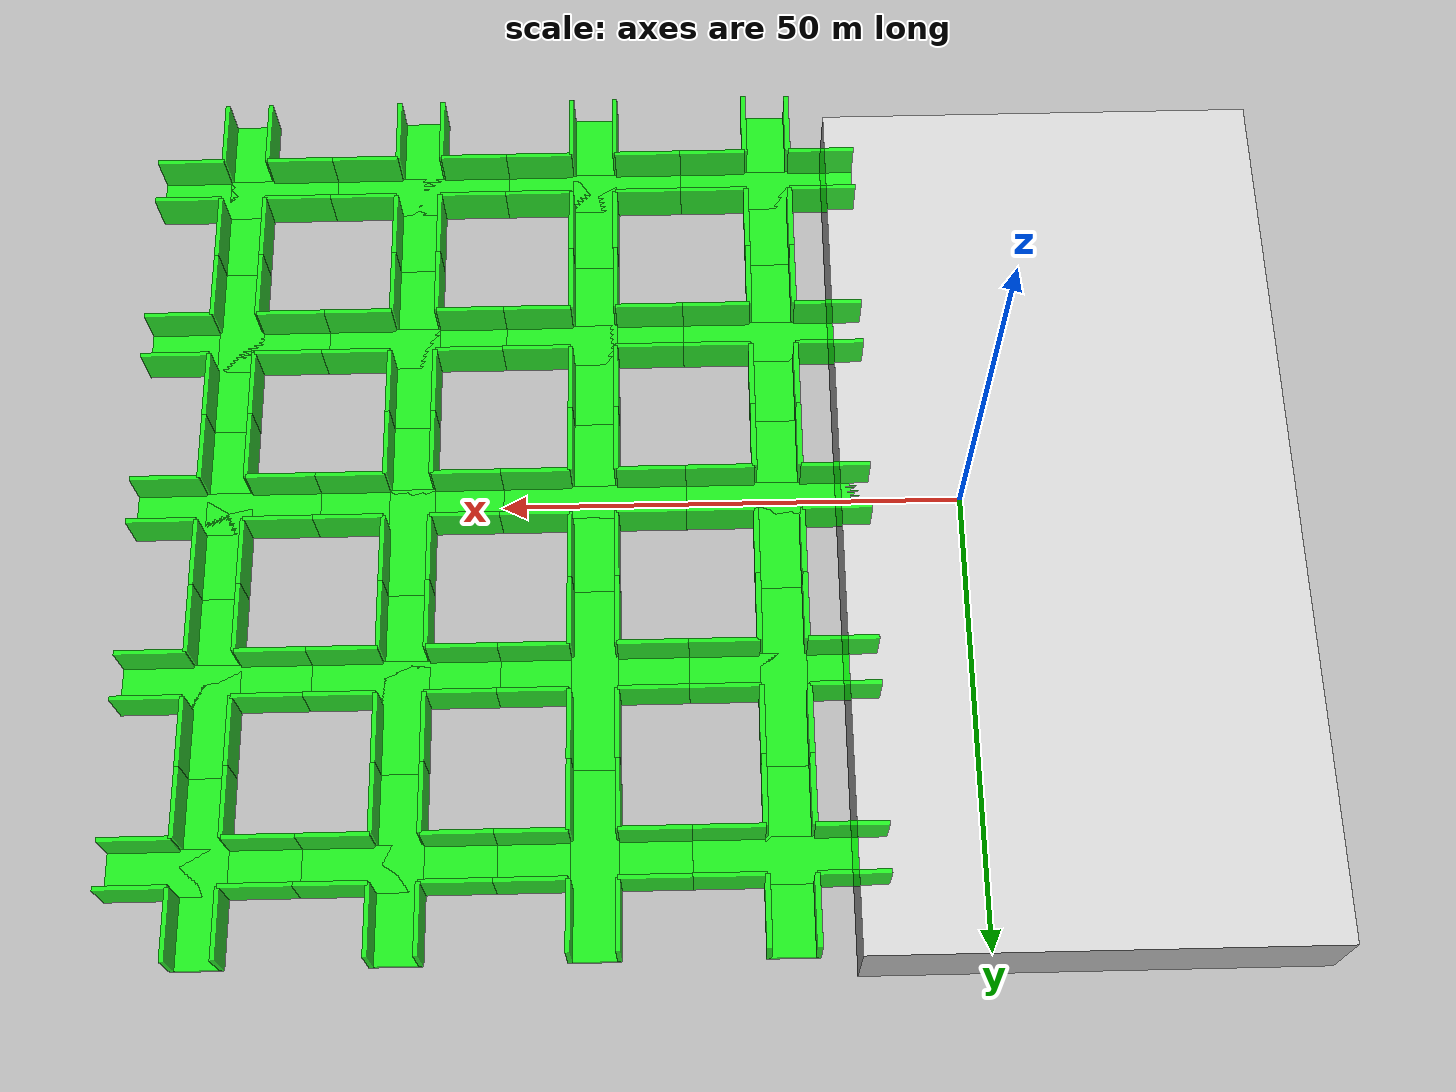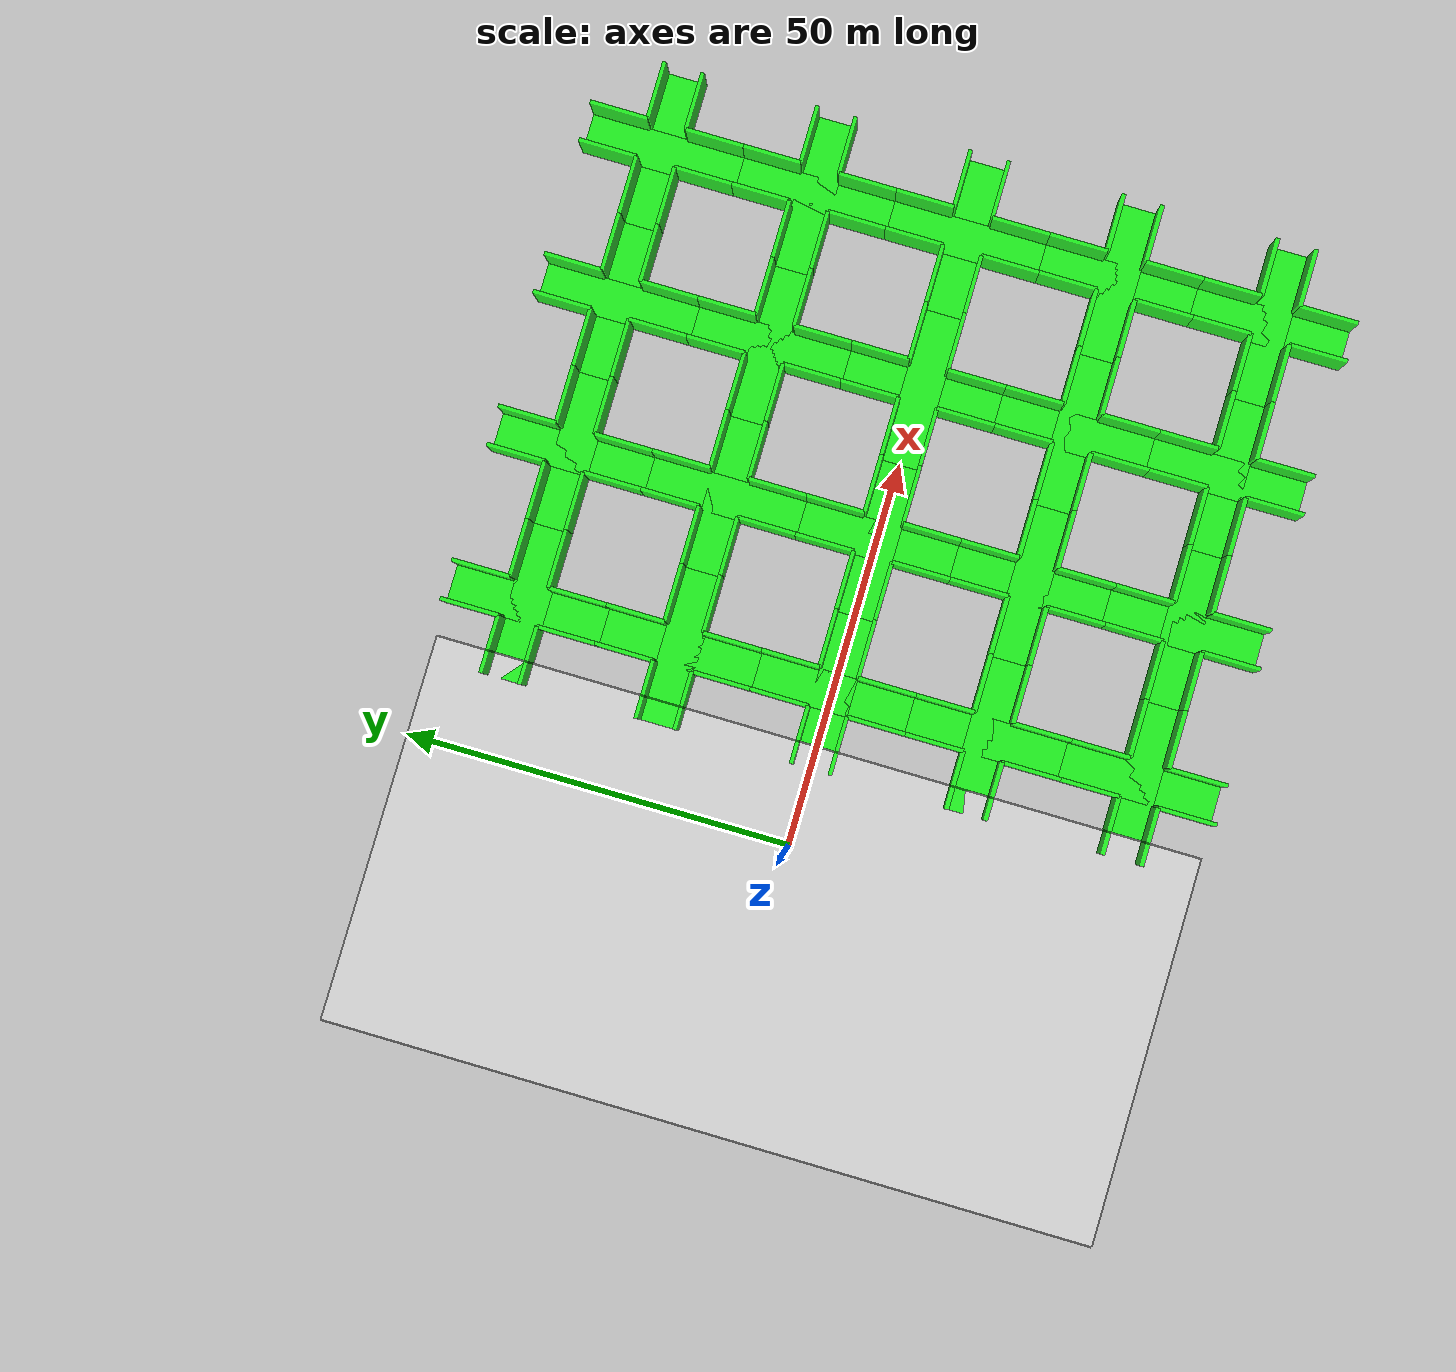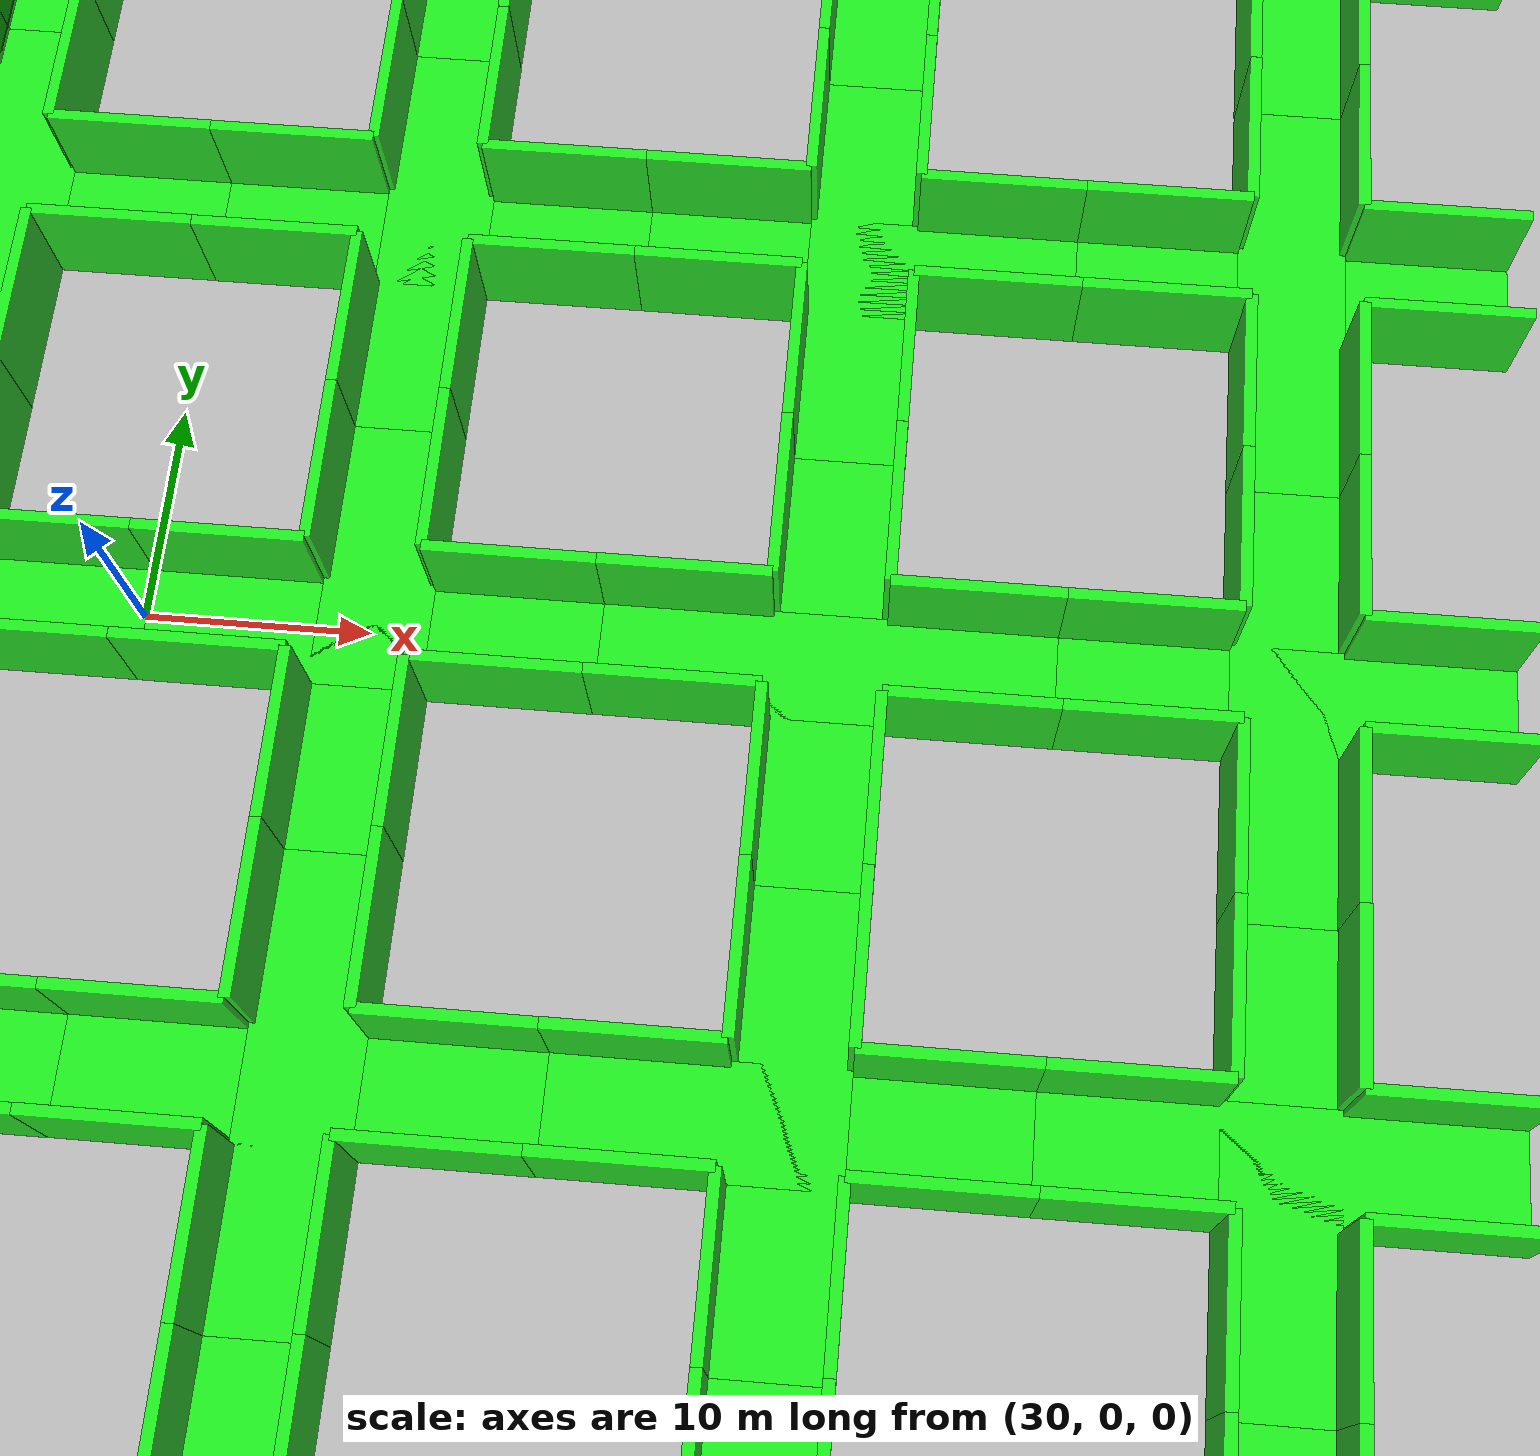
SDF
<sdf version="1.9">
 <world name="levels">
  <plugin name="ignition::gazebo::systems::Physics" filename="ignition-gazebo-physics-system"/>
  <plugin name="ignition::gazebo::systems::UserCommands" filename="ignition-gazebo-user-commands-system"/>
  <plugin name="ignition::gazebo::systems::SceneBroadcaster" filename="ignition-gazebo-scene-broadcaster-system"/>
  <plugin name="ignition::gazebo::systems::Imu" filename="ignition-gazebo-imu-system"/>
  <plugin name="ignition::gazebo::systems::Sensors" filename="ignition-gazebo-sensors-system">
   <render_engine>ogre</render_engine>
  </plugin>
  <scene>
   <ambient>0.8 0.8 0.8 1</ambient>
   <background>0.34 0.39 0.43 1</background>
   <grid>false</grid>
   <origin_visual>false</origin_visual>
   <shadows>true</shadows>
  </scene>
  <plugin name="ignition::gazebo" filename="dummy">
   <level name="level0">
    <pose>20 -40 2.5 0 0 0</pose>
    <geometry><box><size>40 40 1000</size></box></geometry>
    <ref>tile_1</ref>
   </level>
   <level name="level1">
    <pose>20 -20 2.5 0 0 0</pose>
    <geometry><box><size>40 40 1000</size></box></geometry>
    <ref>tile_2</ref>
   </level>
   <level name="level3">
    <pose>20 20 2.5 0 0 0</pose>
    <geometry><box><size>40 40 1000</size></box></geometry>
    <ref>tile_4</ref>
   </level>
   <level name="level4">
    <pose>20 40 2.5 0 0 0</pose>
    <geometry><box><size>40 40 1000</size></box></geometry>
    <ref>tile_5</ref>
   </level>
   <level name="level5">
    <pose>40 -40 2.5 0 0 0</pose>
    <geometry><box><size>40 40 1000</size></box></geometry>
    <ref>tile_6</ref>
   </level>
   <level name="level6">
    <pose>40 -20 2.5 0 0 0</pose>
    <geometry><box><size>40 40 1000</size></box></geometry>
    <ref>tile_7</ref>
   </level>
   <level name="level7">
    <pose>40 0 2.5 0 0 0</pose>
    <geometry><box><size>40 40 1000</size></box></geometry>
    <ref>tile_8</ref>
   </level>
   <level name="level8">
    <pose>40 20 2.5 0 0 0</pose>
    <geometry><box><size>40 40 1000</size></box></geometry>
    <ref>tile_9</ref>
   </level>
   <level name="level9">
    <pose>40 40 2.5 0 0 0</pose>
    <geometry><box><size>40 40 1000</size></box></geometry>
    <ref>tile_10</ref>
   </level>
   <level name="level10">
    <pose>60 -40 2.5 0 0 0</pose>
    <geometry><box><size>40 40 1000</size></box></geometry>
    <ref>tile_11</ref>
   </level>
   <level name="level11">
    <pose>60 -20 2.5 0 0 0</pose>
    <geometry><box><size>40 40 1000</size></box></geometry>
    <ref>tile_12</ref>
   </level>
   <level name="level12">
    <pose>60 0 2.5 0 0 0</pose>
    <geometry><box><size>40 40 1000</size></box></geometry>
    <ref>tile_13</ref>
   </level>
   <level name="level13">
    <pose>60 20 2.5 0 0 0</pose>
    <geometry><box><size>40 40 1000</size></box></geometry>
    <ref>tile_14</ref>
   </level>
   <level name="level14">
    <pose>60 40 2.5 0 0 0</pose>
    <geometry><box><size>40 40 1000</size></box></geometry>
    <ref>tile_15</ref>
   </level>
   <level name="level15">
    <pose>80 -40 2.5 0 0 0</pose>
    <geometry><box><size>40 40 1000</size></box></geometry>
    <ref>tile_16</ref>
   </level>
   <level name="level16">
    <pose>80 -20 2.5 0 0 0</pose>
    <geometry><box><size>40 40 1000</size></box></geometry>
    <ref>tile_17</ref>
   </level>
   <level name="level17">
    <pose>80 0 2.5 0 0 0</pose>
    <geometry><box><size>40 40 1000</size></box></geometry>
    <ref>tile_18</ref>
   </level>
   <level name="level18">
    <pose>80 20 2.5 0 0 0</pose>
    <geometry><box><size>40 40 1000</size></box></geometry>
    <ref>tile_19</ref>
   </level>
   <level name="level19">
    <pose>80 40 2.5 0 0 0</pose>
    <geometry><box><size>40 40 1000</size></box></geometry>
    <ref>tile_20</ref>
   </level>
  </plugin>
  <gravity>0 0 -9.8</gravity>
  <magnetic_field>6e-06 2.3e-05 -4.2e-05</magnetic_field>
  <atmosphere type="adiabatic"/>
  <physics type="ode">
   <max_step_size>0.001</max_step_size>
   <real_time_factor>1</real_time_factor>
   <real_time_update_rate>1000</real_time_update_rate>
  </physics>
  <model name="stage">
   <pose>-12 0 -5 0 -0 0</pose>
   <static>true</static>
   <link name="link">
    <collision name="collision"><geometry><box><size>50 100 10</size></box></geometry></collision>
    <visual name="visual">
     <geometry><box><size>50 100 10</size></box></geometry>
     <material>
      <ambient>0.8 0.8 0.8 1</ambient>
      <diffuse>0.8 0.8 0.8 1</diffuse>
      <specular>0.8 0.8 0.8 1</specular>
     </material>
    </visual>
    <inertial>
     <mass>1</mass>
     <inertia><ixx>1</ixx><ixy>0</ixy><ixz>0</ixz><iyy>1</iyy><iyz>0</iyz><izz>1</izz></inertia>
    </inertial>
   </link>
  </model>
  <model name="tile_1">
   <pose>20 -40 0 0 0 -1.5708</pose>
   <static>true</static>
   <link name="link">
    <collision name="collision_0">
     <pose>0 0 -0.25 0 0 0</pose>
     <geometry><box><size>5 20 0.5</size></box></geometry>
    </collision>
    <visual name="visual_0">
     <pose>0 0 -0.25 0 0 0</pose>
     <geometry><box><size>5 20 0.5</size></box></geometry>
     <material><ambient>0 1 0 0.8</ambient><diffuse>0 1 0 0.8</diffuse><specular>1 1 1 0.8</specular></material>
    </visual>
    <collision name="collision_1">
     <pose>0 0 -0.25 0 0 1.57</pose>
     <geometry><box><size>5 20 0.5</size></box></geometry>
    </collision>
    <visual name="visual_1">
     <pose>0 0 -0.25 0 0 1.57</pose>
     <geometry><box><size>5 20 0.5</size></box></geometry>
     <material><ambient>0 1 0 0.8</ambient><diffuse>0 1 0 0.8</diffuse><specular>1 1 1 0.8</specular></material>
    </visual>
    <collision name="collision_2">
     <pose>-2.5 6.25 2 3.14 -1.57 0</pose>
     <geometry><box><size>5 7.5 0.5</size></box></geometry>
    </collision>
    <visual name="visual_2">
     <pose>-2.5 6.25 2 3.14 -1.57 0</pose>
     <geometry><box><size>5 7.5 0.5</size></box></geometry>
     <material><ambient>0 1 0 0.8</ambient><diffuse>0 1 0 0.8</diffuse><specular>1 1 1 0.8</specular></material>
    </visual>
    <collision name="collision_3">
     <pose>2.5 6.25 2 3.14 -1.57 0</pose>
     <geometry><box><size>5 7.5 0.5</size></box></geometry>
    </collision>
    <visual name="visual_3">
     <pose>2.5 6.25 2 3.14 -1.57 0</pose>
     <geometry><box><size>5 7.5 0.5</size></box></geometry>
     <material><ambient>0 1 0 0.8</ambient><diffuse>0 1 0 0.8</diffuse><specular>1 1 1 0.8</specular></material>
    </visual>
    <collision name="collision_4">
     <pose>-2.5 -6.25 2 3.14 -1.57 0</pose>
     <geometry><box><size>5 7.5 0.5</size></box></geometry>
    </collision>
    <visual name="visual_4">
     <pose>-2.5 -6.25 2 3.14 -1.57 0</pose>
     <geometry><box><size>5 7.5 0.5</size></box></geometry>
     <material><ambient>0 1 0 0.8</ambient><diffuse>0 1 0 0.8</diffuse><specular>1 1 1 0.8</specular></material>
    </visual>
    <collision name="collision_5">
     <pose>2.5 -6.25 2 3.14 -1.57 0</pose>
     <geometry><box><size>5 7.5 0.5</size></box></geometry>
    </collision>
    <visual name="visual_5">
     <pose>2.5 -6.25 2 3.14 -1.57 0</pose>
     <geometry><box><size>5 7.5 0.5</size></box></geometry>
     <material><ambient>0 1 0 0.8</ambient><diffuse>0 1 0 0.8</diffuse><specular>1 1 1 0.8</specular></material>
    </visual>
    <collision name="collision_6">
     <pose>6.25 2.5 2 1.57 1.57 0</pose>
     <geometry><box><size>5 7.5 0.5</size></box></geometry>
    </collision>
    <visual name="visual_6">
     <pose>6.25 2.5 2 1.57 1.57 0</pose>
     <geometry><box><size>5 7.5 0.5</size></box></geometry>
     <material><ambient>0 1 0 0.8</ambient><diffuse>0 1 0 0.8</diffuse><specular>1 1 1 0.8</specular></material>
    </visual>
    <collision name="collision_7">
     <pose>-6.25 2.5 2 1.57 1.57 0</pose>
     <geometry><box><size>5 7.5 0.5</size></box></geometry>
    </collision>
    <visual name="visual_7">
     <pose>-6.25 2.5 2 1.57 1.57 0</pose>
     <geometry><box><size>5 7.5 0.5</size></box></geometry>
     <material><ambient>0 1 0 0.8</ambient><diffuse>0 1 0 0.8</diffuse><specular>1 1 1 0.8</specular></material>
    </visual>
    <collision name="collision_8">
     <pose>6.25 -2.5 2 1.57 1.57 0</pose>
     <geometry><box><size>5 7.5 0.5</size></box></geometry>
    </collision>
    <visual name="visual_8">
     <pose>6.25 -2.5 2 1.57 1.57 0</pose>
     <geometry><box><size>5 7.5 0.5</size></box></geometry>
     <material><ambient>0 1 0 0.8</ambient><diffuse>0 1 0 0.8</diffuse><specular>1 1 1 0.8</specular></material>
    </visual>
    <collision name="collision_9">
     <pose>-6.25 -2.5 2 1.57 1.57 0</pose>
     <geometry><box><size>5 7.5 0.5</size></box></geometry>
    </collision>
    <visual name="visual_9">
     <pose>-6.25 -2.5 2 1.57 1.57 0</pose>
     <geometry><box><size>5 7.5 0.5</size></box></geometry>
     <material><ambient>0 1 0 0.8</ambient><diffuse>0 1 0 0.8</diffuse><specular>1 1 1 0.8</specular></material>
    </visual>
    <inertial>
     <mass>1</mass>
     <inertia><ixx>1</ixx><ixy>0</ixy><ixz>0</ixz><iyy>1</iyy><iyz>0</iyz><izz>1</izz></inertia>
    </inertial>
   </link>
  </model>
  <model name="tile_2">
   <pose>20 -20 0 0 0 -1.5708</pose>
   <static>true</static>
   <link name="link">
    <collision name="collision_0">
     <pose>0 0 -0.25 0 0 0</pose>
     <geometry><box><size>5 20 0.5</size></box></geometry>
    </collision>
    <visual name="visual_0">
     <pose>0 0 -0.25 0 0 0</pose>
     <geometry><box><size>5 20 0.5</size></box></geometry>
     <material><ambient>0 1 0 0.8</ambient><diffuse>0 1 0 0.8</diffuse><specular>1 1 1 0.8</specular></material>
    </visual>
    <collision name="collision_1">
     <pose>0 0 -0.25 0 0 1.57</pose>
     <geometry><box><size>5 20 0.5</size></box></geometry>
    </collision>
    <visual name="visual_1">
     <pose>0 0 -0.25 0 0 1.57</pose>
     <geometry><box><size>5 20 0.5</size></box></geometry>
     <material><ambient>0 1 0 0.8</ambient><diffuse>0 1 0 0.8</diffuse><specular>1 1 1 0.8</specular></material>
    </visual>
    <collision name="collision_2">
     <pose>-2.5 6.25 2 3.14 -1.57 0</pose>
     <geometry><box><size>5 7.5 0.5</size></box></geometry>
    </collision>
    <visual name="visual_2">
     <pose>-2.5 6.25 2 3.14 -1.57 0</pose>
     <geometry><box><size>5 7.5 0.5</size></box></geometry>
     <material><ambient>0 1 0 0.8</ambient><diffuse>0 1 0 0.8</diffuse><specular>1 1 1 0.8</specular></material>
    </visual>
    <collision name="collision_3">
     <pose>2.5 6.25 2 3.14 -1.57 0</pose>
     <geometry><box><size>5 7.5 0.5</size></box></geometry>
    </collision>
    <visual name="visual_3">
     <pose>2.5 6.25 2 3.14 -1.57 0</pose>
     <geometry><box><size>5 7.5 0.5</size></box></geometry>
     <material><ambient>0 1 0 0.8</ambient><diffuse>0 1 0 0.8</diffuse><specular>1 1 1 0.8</specular></material>
    </visual>
    <collision name="collision_4">
     <pose>-2.5 -6.25 2 3.14 -1.57 0</pose>
     <geometry><box><size>5 7.5 0.5</size></box></geometry>
    </collision>
    <visual name="visual_4">
     <pose>-2.5 -6.25 2 3.14 -1.57 0</pose>
     <geometry><box><size>5 7.5 0.5</size></box></geometry>
     <material><ambient>0 1 0 0.8</ambient><diffuse>0 1 0 0.8</diffuse><specular>1 1 1 0.8</specular></material>
    </visual>
    <collision name="collision_5">
     <pose>2.5 -6.25 2 3.14 -1.57 0</pose>
     <geometry><box><size>5 7.5 0.5</size></box></geometry>
    </collision>
    <visual name="visual_5">
     <pose>2.5 -6.25 2 3.14 -1.57 0</pose>
     <geometry><box><size>5 7.5 0.5</size></box></geometry>
     <material><ambient>0 1 0 0.8</ambient><diffuse>0 1 0 0.8</diffuse><specular>1 1 1 0.8</specular></material>
    </visual>
    <collision name="collision_6">
     <pose>6.25 2.5 2 1.57 1.57 0</pose>
     <geometry><box><size>5 7.5 0.5</size></box></geometry>
    </collision>
    <visual name="visual_6">
     <pose>6.25 2.5 2 1.57 1.57 0</pose>
     <geometry><box><size>5 7.5 0.5</size></box></geometry>
     <material><ambient>0 1 0 0.8</ambient><diffuse>0 1 0 0.8</diffuse><specular>1 1 1 0.8</specular></material>
    </visual>
    <collision name="collision_7">
     <pose>-6.25 2.5 2 1.57 1.57 0</pose>
     <geometry><box><size>5 7.5 0.5</size></box></geometry>
    </collision>
    <visual name="visual_7">
     <pose>-6.25 2.5 2 1.57 1.57 0</pose>
     <geometry><box><size>5 7.5 0.5</size></box></geometry>
     <material><ambient>0 1 0 0.8</ambient><diffuse>0 1 0 0.8</diffuse><specular>1 1 1 0.8</specular></material>
    </visual>
    <collision name="collision_8">
     <pose>6.25 -2.5 2 1.57 1.57 0</pose>
     <geometry><box><size>5 7.5 0.5</size></box></geometry>
    </collision>
    <visual name="visual_8">
     <pose>6.25 -2.5 2 1.57 1.57 0</pose>
     <geometry><box><size>5 7.5 0.5</size></box></geometry>
     <material><ambient>0 1 0 0.8</ambient><diffuse>0 1 0 0.8</diffuse><specular>1 1 1 0.8</specular></material>
    </visual>
    <collision name="collision_9">
     <pose>-6.25 -2.5 2 1.57 1.57 0</pose>
     <geometry><box><size>5 7.5 0.5</size></box></geometry>
    </collision>
    <visual name="visual_9">
     <pose>-6.25 -2.5 2 1.57 1.57 0</pose>
     <geometry><box><size>5 7.5 0.5</size></box></geometry>
     <material><ambient>0 1 0 0.8</ambient><diffuse>0 1 0 0.8</diffuse><specular>1 1 1 0.8</specular></material>
    </visual>
    <inertial>
     <mass>1</mass>
     <inertia><ixx>1</ixx><ixy>0</ixy><ixz>0</ixz><iyy>1</iyy><iyz>0</iyz><izz>1</izz></inertia>
    </inertial>
   </link>
  </model>
  <model name="tile_3">
   <pose>20 0 0 0 -0 0</pose>
   <static>true</static>
   <link name="link">
    <collision name="collision_0">
     <pose>0 0 -0.25 0 0 0</pose>
     <geometry><box><size>5 20 0.5</size></box></geometry>
    </collision>
    <visual name="visual_0">
     <pose>0 0 -0.25 0 0 0</pose>
     <geometry><box><size>5 20 0.5</size></box></geometry>
     <material><ambient>0 1 0 0.8</ambient><diffuse>0 1 0 0.8</diffuse><specular>1 1 1 0.8</specular></material>
    </visual>
    <collision name="collision_1">
     <pose>0 0 -0.25 0 0 1.57</pose>
     <geometry><box><size>5 20 0.5</size></box></geometry>
    </collision>
    <visual name="visual_1">
     <pose>0 0 -0.25 0 0 1.57</pose>
     <geometry><box><size>5 20 0.5</size></box></geometry>
     <material><ambient>0 1 0 0.8</ambient><diffuse>0 1 0 0.8</diffuse><specular>1 1 1 0.8</specular></material>
    </visual>
    <collision name="collision_2">
     <pose>-2.5 6.25 2 3.14 -1.57 0</pose>
     <geometry><box><size>5 7.5 0.5</size></box></geometry>
    </collision>
    <visual name="visual_2">
     <pose>-2.5 6.25 2 3.14 -1.57 0</pose>
     <geometry><box><size>5 7.5 0.5</size></box></geometry>
     <material><ambient>0 1 0 0.8</ambient><diffuse>0 1 0 0.8</diffuse><specular>1 1 1 0.8</specular></material>
    </visual>
    <collision name="collision_3">
     <pose>2.5 6.25 2 3.14 -1.57 0</pose>
     <geometry><box><size>5 7.5 0.5</size></box></geometry>
    </collision>
    <visual name="visual_3">
     <pose>2.5 6.25 2 3.14 -1.57 0</pose>
     <geometry><box><size>5 7.5 0.5</size></box></geometry>
     <material><ambient>0 1 0 0.8</ambient><diffuse>0 1 0 0.8</diffuse><specular>1 1 1 0.8</specular></material>
    </visual>
    <collision name="collision_4">
     <pose>-2.5 -6.25 2 3.14 -1.57 0</pose>
     <geometry><box><size>5 7.5 0.5</size></box></geometry>
    </collision>
    <visual name="visual_4">
     <pose>-2.5 -6.25 2 3.14 -1.57 0</pose>
     <geometry><box><size>5 7.5 0.5</size></box></geometry>
     <material><ambient>0 1 0 0.8</ambient><diffuse>0 1 0 0.8</diffuse><specular>1 1 1 0.8</specular></material>
    </visual>
    <collision name="collision_5">
     <pose>2.5 -6.25 2 3.14 -1.57 0</pose>
     <geometry><box><size>5 7.5 0.5</size></box></geometry>
    </collision>
    <visual name="visual_5">
     <pose>2.5 -6.25 2 3.14 -1.57 0</pose>
     <geometry><box><size>5 7.5 0.5</size></box></geometry>
     <material><ambient>0 1 0 0.8</ambient><diffuse>0 1 0 0.8</diffuse><specular>1 1 1 0.8</specular></material>
    </visual>
    <collision name="collision_6">
     <pose>6.25 2.5 2 1.57 1.57 0</pose>
     <geometry><box><size>5 7.5 0.5</size></box></geometry>
    </collision>
    <visual name="visual_6">
     <pose>6.25 2.5 2 1.57 1.57 0</pose>
     <geometry><box><size>5 7.5 0.5</size></box></geometry>
     <material><ambient>0 1 0 0.8</ambient><diffuse>0 1 0 0.8</diffuse><specular>1 1 1 0.8</specular></material>
    </visual>
    <collision name="collision_7">
     <pose>-6.25 2.5 2 1.57 1.57 0</pose>
     <geometry><box><size>5 7.5 0.5</size></box></geometry>
    </collision>
    <visual name="visual_7">
     <pose>-6.25 2.5 2 1.57 1.57 0</pose>
     <geometry><box><size>5 7.5 0.5</size></box></geometry>
     <material><ambient>0 1 0 0.8</ambient><diffuse>0 1 0 0.8</diffuse><specular>1 1 1 0.8</specular></material>
    </visual>
    <collision name="collision_8">
     <pose>6.25 -2.5 2 1.57 1.57 0</pose>
     <geometry><box><size>5 7.5 0.5</size></box></geometry>
    </collision>
    <visual name="visual_8">
     <pose>6.25 -2.5 2 1.57 1.57 0</pose>
     <geometry><box><size>5 7.5 0.5</size></box></geometry>
     <material><ambient>0 1 0 0.8</ambient><diffuse>0 1 0 0.8</diffuse><specular>1 1 1 0.8</specular></material>
    </visual>
    <collision name="collision_9">
     <pose>-6.25 -2.5 2 1.57 1.57 0</pose>
     <geometry><box><size>5 7.5 0.5</size></box></geometry>
    </collision>
    <visual name="visual_9">
     <pose>-6.25 -2.5 2 1.57 1.57 0</pose>
     <geometry><box><size>5 7.5 0.5</size></box></geometry>
     <material><ambient>0 1 0 0.8</ambient><diffuse>0 1 0 0.8</diffuse><specular>1 1 1 0.8</specular></material>
    </visual>
    <inertial>
     <mass>1</mass>
     <inertia><ixx>1</ixx><ixy>0</ixy><ixz>0</ixz><iyy>1</iyy><iyz>0</iyz><izz>1</izz></inertia>
    </inertial>
   </link>
  </model>
  <model name="tile_4">
   <pose>20 20 0 0 -0 0</pose>
   <static>true</static>
   <link name="link">
    <collision name="collision_0">
     <pose>0 0 -0.25 0 0 0</pose>
     <geometry><box><size>5 20 0.5</size></box></geometry>
    </collision>
    <visual name="visual_0">
     <pose>0 0 -0.25 0 0 0</pose>
     <geometry><box><size>5 20 0.5</size></box></geometry>
     <material><ambient>0 1 0 0.8</ambient><diffuse>0 1 0 0.8</diffuse><specular>1 1 1 0.8</specular></material>
    </visual>
    <collision name="collision_1">
     <pose>0 0 -0.25 0 0 1.57</pose>
     <geometry><box><size>5 20 0.5</size></box></geometry>
    </collision>
    <visual name="visual_1">
     <pose>0 0 -0.25 0 0 1.57</pose>
     <geometry><box><size>5 20 0.5</size></box></geometry>
     <material><ambient>0 1 0 0.8</ambient><diffuse>0 1 0 0.8</diffuse><specular>1 1 1 0.8</specular></material>
    </visual>
    <collision name="collision_2">
     <pose>-2.5 6.25 2 3.14 -1.57 0</pose>
     <geometry><box><size>5 7.5 0.5</size></box></geometry>
    </collision>
    <visual name="visual_2">
     <pose>-2.5 6.25 2 3.14 -1.57 0</pose>
     <geometry><box><size>5 7.5 0.5</size></box></geometry>
     <material><ambient>0 1 0 0.8</ambient><diffuse>0 1 0 0.8</diffuse><specular>1 1 1 0.8</specular></material>
    </visual>
    <collision name="collision_3">
     <pose>2.5 6.25 2 3.14 -1.57 0</pose>
     <geometry><box><size>5 7.5 0.5</size></box></geometry>
    </collision>
    <visual name="visual_3">
     <pose>2.5 6.25 2 3.14 -1.57 0</pose>
     <geometry><box><size>5 7.5 0.5</size></box></geometry>
     <material><ambient>0 1 0 0.8</ambient><diffuse>0 1 0 0.8</diffuse><specular>1 1 1 0.8</specular></material>
    </visual>
    <collision name="collision_4">
     <pose>-2.5 -6.25 2 3.14 -1.57 0</pose>
     <geometry><box><size>5 7.5 0.5</size></box></geometry>
    </collision>
    <visual name="visual_4">
     <pose>-2.5 -6.25 2 3.14 -1.57 0</pose>
     <geometry><box><size>5 7.5 0.5</size></box></geometry>
     <material><ambient>0 1 0 0.8</ambient><diffuse>0 1 0 0.8</diffuse><specular>1 1 1 0.8</specular></material>
    </visual>
    <collision name="collision_5">
     <pose>2.5 -6.25 2 3.14 -1.57 0</pose>
     <geometry><box><size>5 7.5 0.5</size></box></geometry>
    </collision>
    <visual name="visual_5">
     <pose>2.5 -6.25 2 3.14 -1.57 0</pose>
     <geometry><box><size>5 7.5 0.5</size></box></geometry>
     <material><ambient>0 1 0 0.8</ambient><diffuse>0 1 0 0.8</diffuse><specular>1 1 1 0.8</specular></material>
    </visual>
    <collision name="collision_6">
     <pose>6.25 2.5 2 1.57 1.57 0</pose>
     <geometry><box><size>5 7.5 0.5</size></box></geometry>
    </collision>
    <visual name="visual_6">
     <pose>6.25 2.5 2 1.57 1.57 0</pose>
     <geometry><box><size>5 7.5 0.5</size></box></geometry>
     <material><ambient>0 1 0 0.8</ambient><diffuse>0 1 0 0.8</diffuse><specular>1 1 1 0.8</specular></material>
    </visual>
    <collision name="collision_7">
     <pose>-6.25 2.5 2 1.57 1.57 0</pose>
     <geometry><box><size>5 7.5 0.5</size></box></geometry>
    </collision>
    <visual name="visual_7">
     <pose>-6.25 2.5 2 1.57 1.57 0</pose>
     <geometry><box><size>5 7.5 0.5</size></box></geometry>
     <material><ambient>0 1 0 0.8</ambient><diffuse>0 1 0 0.8</diffuse><specular>1 1 1 0.8</specular></material>
    </visual>
    <collision name="collision_8">
     <pose>6.25 -2.5 2 1.57 1.57 0</pose>
     <geometry><box><size>5 7.5 0.5</size></box></geometry>
    </collision>
    <visual name="visual_8">
     <pose>6.25 -2.5 2 1.57 1.57 0</pose>
     <geometry><box><size>5 7.5 0.5</size></box></geometry>
     <material><ambient>0 1 0 0.8</ambient><diffuse>0 1 0 0.8</diffuse><specular>1 1 1 0.8</specular></material>
    </visual>
    <collision name="collision_9">
     <pose>-6.25 -2.5 2 1.57 1.57 0</pose>
     <geometry><box><size>5 7.5 0.5</size></box></geometry>
    </collision>
    <visual name="visual_9">
     <pose>-6.25 -2.5 2 1.57 1.57 0</pose>
     <geometry><box><size>5 7.5 0.5</size></box></geometry>
     <material><ambient>0 1 0 0.8</ambient><diffuse>0 1 0 0.8</diffuse><specular>1 1 1 0.8</specular></material>
    </visual>
    <inertial>
     <mass>1</mass>
     <inertia><ixx>1</ixx><ixy>0</ixy><ixz>0</ixz><iyy>1</iyy><iyz>0</iyz><izz>1</izz></inertia>
    </inertial>
   </link>
  </model>
  <model name="tile_5">
   <pose>20 40 0 0 0 -1.5708</pose>
   <static>true</static>
   <link name="link">
    <collision name="collision_0">
     <pose>0 0 -0.25 0 0 0</pose>
     <geometry><box><size>5 20 0.5</size></box></geometry>
    </collision>
    <visual name="visual_0">
     <pose>0 0 -0.25 0 0 0</pose>
     <geometry><box><size>5 20 0.5</size></box></geometry>
     <material><ambient>0 1 0 0.8</ambient><diffuse>0 1 0 0.8</diffuse><specular>1 1 1 0.8</specular></material>
    </visual>
    <collision name="collision_1">
     <pose>0 0 -0.25 0 0 1.57</pose>
     <geometry><box><size>5 20 0.5</size></box></geometry>
    </collision>
    <visual name="visual_1">
     <pose>0 0 -0.25 0 0 1.57</pose>
     <geometry><box><size>5 20 0.5</size></box></geometry>
     <material><ambient>0 1 0 0.8</ambient><diffuse>0 1 0 0.8</diffuse><specular>1 1 1 0.8</specular></material>
    </visual>
    <collision name="collision_2">
     <pose>-2.5 6.25 2 3.14 -1.57 0</pose>
     <geometry><box><size>5 7.5 0.5</size></box></geometry>
    </collision>
    <visual name="visual_2">
     <pose>-2.5 6.25 2 3.14 -1.57 0</pose>
     <geometry><box><size>5 7.5 0.5</size></box></geometry>
     <material><ambient>0 1 0 0.8</ambient><diffuse>0 1 0 0.8</diffuse><specular>1 1 1 0.8</specular></material>
    </visual>
    <collision name="collision_3">
     <pose>2.5 6.25 2 3.14 -1.57 0</pose>
     <geometry><box><size>5 7.5 0.5</size></box></geometry>
    </collision>
    <visual name="visual_3">
     <pose>2.5 6.25 2 3.14 -1.57 0</pose>
     <geometry><box><size>5 7.5 0.5</size></box></geometry>
     <material><ambient>0 1 0 0.8</ambient><diffuse>0 1 0 0.8</diffuse><specular>1 1 1 0.8</specular></material>
    </visual>
    <collision name="collision_4">
     <pose>-2.5 -6.25 2 3.14 -1.57 0</pose>
     <geometry><box><size>5 7.5 0.5</size></box></geometry>
    </collision>
    <visual name="visual_4">
     <pose>-2.5 -6.25 2 3.14 -1.57 0</pose>
     <geometry><box><size>5 7.5 0.5</size></box></geometry>
     <material><ambient>0 1 0 0.8</ambient><diffuse>0 1 0 0.8</diffuse><specular>1 1 1 0.8</specular></material>
    </visual>
    <collision name="collision_5">
     <pose>2.5 -6.25 2 3.14 -1.57 0</pose>
     <geometry><box><size>5 7.5 0.5</size></box></geometry>
    </collision>
    <visual name="visual_5">
     <pose>2.5 -6.25 2 3.14 -1.57 0</pose>
     <geometry><box><size>5 7.5 0.5</size></box></geometry>
     <material><ambient>0 1 0 0.8</ambient><diffuse>0 1 0 0.8</diffuse><specular>1 1 1 0.8</specular></material>
    </visual>
    <collision name="collision_6">
     <pose>6.25 2.5 2 1.57 1.57 0</pose>
     <geometry><box><size>5 7.5 0.5</size></box></geometry>
    </collision>
    <visual name="visual_6">
     <pose>6.25 2.5 2 1.57 1.57 0</pose>
     <geometry><box><size>5 7.5 0.5</size></box></geometry>
     <material><ambient>0 1 0 0.8</ambient><diffuse>0 1 0 0.8</diffuse><specular>1 1 1 0.8</specular></material>
    </visual>
    <collision name="collision_7">
     <pose>-6.25 2.5 2 1.57 1.57 0</pose>
     <geometry><box><size>5 7.5 0.5</size></box></geometry>
    </collision>
    <visual name="visual_7">
     <pose>-6.25 2.5 2 1.57 1.57 0</pose>
     <geometry><box><size>5 7.5 0.5</size></box></geometry>
     <material><ambient>0 1 0 0.8</ambient><diffuse>0 1 0 0.8</diffuse><specular>1 1 1 0.8</specular></material>
    </visual>
    <collision name="collision_8">
     <pose>6.25 -2.5 2 1.57 1.57 0</pose>
     <geometry><box><size>5 7.5 0.5</size></box></geometry>
    </collision>
    <visual name="visual_8">
     <pose>6.25 -2.5 2 1.57 1.57 0</pose>
     <geometry><box><size>5 7.5 0.5</size></box></geometry>
     <material><ambient>0 1 0 0.8</ambient><diffuse>0 1 0 0.8</diffuse><specular>1 1 1 0.8</specular></material>
    </visual>
    <collision name="collision_9">
     <pose>-6.25 -2.5 2 1.57 1.57 0</pose>
     <geometry><box><size>5 7.5 0.5</size></box></geometry>
    </collision>
    <visual name="visual_9">
     <pose>-6.25 -2.5 2 1.57 1.57 0</pose>
     <geometry><box><size>5 7.5 0.5</size></box></geometry>
     <material><ambient>0 1 0 0.8</ambient><diffuse>0 1 0 0.8</diffuse><specular>1 1 1 0.8</specular></material>
    </visual>
    <inertial>
     <mass>1</mass>
     <inertia><ixx>1</ixx><ixy>0</ixy><ixz>0</ixz><iyy>1</iyy><iyz>0</iyz><izz>1</izz></inertia>
    </inertial>
   </link>
  </model>
  <model name="tile_6">
   <pose>40 -40 0 0 -0 0</pose>
   <static>true</static>
   <link name="link">
    <collision name="collision_0">
     <pose>0 0 -0.25 0 0 0</pose>
     <geometry><box><size>5 20 0.5</size></box></geometry>
    </collision>
    <visual name="visual_0">
     <pose>0 0 -0.25 0 0 0</pose>
     <geometry><box><size>5 20 0.5</size></box></geometry>
     <material><ambient>0 1 0 0.8</ambient><diffuse>0 1 0 0.8</diffuse><specular>1 1 1 0.8</specular></material>
    </visual>
    <collision name="collision_1">
     <pose>0 0 -0.25 0 0 1.57</pose>
     <geometry><box><size>5 20 0.5</size></box></geometry>
    </collision>
    <visual name="visual_1">
     <pose>0 0 -0.25 0 0 1.57</pose>
     <geometry><box><size>5 20 0.5</size></box></geometry>
     <material><ambient>0 1 0 0.8</ambient><diffuse>0 1 0 0.8</diffuse><specular>1 1 1 0.8</specular></material>
    </visual>
    <collision name="collision_2">
     <pose>-2.5 6.25 2 3.14 -1.57 0</pose>
     <geometry><box><size>5 7.5 0.5</size></box></geometry>
    </collision>
    <visual name="visual_2">
     <pose>-2.5 6.25 2 3.14 -1.57 0</pose>
     <geometry><box><size>5 7.5 0.5</size></box></geometry>
     <material><ambient>0 1 0 0.8</ambient><diffuse>0 1 0 0.8</diffuse><specular>1 1 1 0.8</specular></material>
    </visual>
    <collision name="collision_3">
     <pose>2.5 6.25 2 3.14 -1.57 0</pose>
     <geometry><box><size>5 7.5 0.5</size></box></geometry>
    </collision>
    <visual name="visual_3">
     <pose>2.5 6.25 2 3.14 -1.57 0</pose>
     <geometry><box><size>5 7.5 0.5</size></box></geometry>
     <material><ambient>0 1 0 0.8</ambient><diffuse>0 1 0 0.8</diffuse><specular>1 1 1 0.8</specular></material>
    </visual>
    <collision name="collision_4">
     <pose>-2.5 -6.25 2 3.14 -1.57 0</pose>
     <geometry><box><size>5 7.5 0.5</size></box></geometry>
    </collision>
    <visual name="visual_4">
     <pose>-2.5 -6.25 2 3.14 -1.57 0</pose>
     <geometry><box><size>5 7.5 0.5</size></box></geometry>
     <material><ambient>0 1 0 0.8</ambient><diffuse>0 1 0 0.8</diffuse><specular>1 1 1 0.8</specular></material>
    </visual>
    <collision name="collision_5">
     <pose>2.5 -6.25 2 3.14 -1.57 0</pose>
     <geometry><box><size>5 7.5 0.5</size></box></geometry>
    </collision>
    <visual name="visual_5">
     <pose>2.5 -6.25 2 3.14 -1.57 0</pose>
     <geometry><box><size>5 7.5 0.5</size></box></geometry>
     <material><ambient>0 1 0 0.8</ambient><diffuse>0 1 0 0.8</diffuse><specular>1 1 1 0.8</specular></material>
    </visual>
    <collision name="collision_6">
     <pose>6.25 2.5 2 1.57 1.57 0</pose>
     <geometry><box><size>5 7.5 0.5</size></box></geometry>
    </collision>
    <visual name="visual_6">
     <pose>6.25 2.5 2 1.57 1.57 0</pose>
     <geometry><box><size>5 7.5 0.5</size></box></geometry>
     <material><ambient>0 1 0 0.8</ambient><diffuse>0 1 0 0.8</diffuse><specular>1 1 1 0.8</specular></material>
    </visual>
    <collision name="collision_7">
     <pose>-6.25 2.5 2 1.57 1.57 0</pose>
     <geometry><box><size>5 7.5 0.5</size></box></geometry>
    </collision>
    <visual name="visual_7">
     <pose>-6.25 2.5 2 1.57 1.57 0</pose>
     <geometry><box><size>5 7.5 0.5</size></box></geometry>
     <material><ambient>0 1 0 0.8</ambient><diffuse>0 1 0 0.8</diffuse><specular>1 1 1 0.8</specular></material>
    </visual>
    <collision name="collision_8">
     <pose>6.25 -2.5 2 1.57 1.57 0</pose>
     <geometry><box><size>5 7.5 0.5</size></box></geometry>
    </collision>
    <visual name="visual_8">
     <pose>6.25 -2.5 2 1.57 1.57 0</pose>
     <geometry><box><size>5 7.5 0.5</size></box></geometry>
     <material><ambient>0 1 0 0.8</ambient><diffuse>0 1 0 0.8</diffuse><specular>1 1 1 0.8</specular></material>
    </visual>
    <collision name="collision_9">
     <pose>-6.25 -2.5 2 1.57 1.57 0</pose>
     <geometry><box><size>5 7.5 0.5</size></box></geometry>
    </collision>
    <visual name="visual_9">
     <pose>-6.25 -2.5 2 1.57 1.57 0</pose>
     <geometry><box><size>5 7.5 0.5</size></box></geometry>
     <material><ambient>0 1 0 0.8</ambient><diffuse>0 1 0 0.8</diffuse><specular>1 1 1 0.8</specular></material>
    </visual>
    <inertial>
     <mass>1</mass>
     <inertia><ixx>1</ixx><ixy>0</ixy><ixz>0</ixz><iyy>1</iyy><iyz>0</iyz><izz>1</izz></inertia>
    </inertial>
   </link>
  </model>
  <model name="tile_7">
   <pose>40 -20 0 0 0 -1.5708</pose>
   <static>true</static>
   <link name="link">
    <collision name="collision_0">
     <pose>0 0 -0.25 0 0 0</pose>
     <geometry><box><size>5 20 0.5</size></box></geometry>
    </collision>
    <visual name="visual_0">
     <pose>0 0 -0.25 0 0 0</pose>
     <geometry><box><size>5 20 0.5</size></box></geometry>
     <material><ambient>0 1 0 0.8</ambient><diffuse>0 1 0 0.8</diffuse><specular>1 1 1 0.8</specular></material>
    </visual>
    <collision name="collision_1">
     <pose>0 0 -0.25 0 0 1.57</pose>
     <geometry><box><size>5 20 0.5</size></box></geometry>
    </collision>
    <visual name="visual_1">
     <pose>0 0 -0.25 0 0 1.57</pose>
     <geometry><box><size>5 20 0.5</size></box></geometry>
     <material><ambient>0 1 0 0.8</ambient><diffuse>0 1 0 0.8</diffuse><specular>1 1 1 0.8</specular></material>
    </visual>
    <collision name="collision_2">
     <pose>-2.5 6.25 2 3.14 -1.57 0</pose>
     <geometry><box><size>5 7.5 0.5</size></box></geometry>
    </collision>
    <visual name="visual_2">
     <pose>-2.5 6.25 2 3.14 -1.57 0</pose>
     <geometry><box><size>5 7.5 0.5</size></box></geometry>
     <material><ambient>0 1 0 0.8</ambient><diffuse>0 1 0 0.8</diffuse><specular>1 1 1 0.8</specular></material>
    </visual>
    <collision name="collision_3">
     <pose>2.5 6.25 2 3.14 -1.57 0</pose>
     <geometry><box><size>5 7.5 0.5</size></box></geometry>
    </collision>
    <visual name="visual_3">
     <pose>2.5 6.25 2 3.14 -1.57 0</pose>
     <geometry><box><size>5 7.5 0.5</size></box></geometry>
     <material><ambient>0 1 0 0.8</ambient><diffuse>0 1 0 0.8</diffuse><specular>1 1 1 0.8</specular></material>
    </visual>
    <collision name="collision_4">
     <pose>-2.5 -6.25 2 3.14 -1.57 0</pose>
     <geometry><box><size>5 7.5 0.5</size></box></geometry>
    </collision>
    <visual name="visual_4">
     <pose>-2.5 -6.25 2 3.14 -1.57 0</pose>
     <geometry><box><size>5 7.5 0.5</size></box></geometry>
     <material><ambient>0 1 0 0.8</ambient><diffuse>0 1 0 0.8</diffuse><specular>1 1 1 0.8</specular></material>
    </visual>
    <collision name="collision_5">
     <pose>2.5 -6.25 2 3.14 -1.57 0</pose>
     <geometry><box><size>5 7.5 0.5</size></box></geometry>
    </collision>
    <visual name="visual_5">
     <pose>2.5 -6.25 2 3.14 -1.57 0</pose>
     <geometry><box><size>5 7.5 0.5</size></box></geometry>
     <material><ambient>0 1 0 0.8</ambient><diffuse>0 1 0 0.8</diffuse><specular>1 1 1 0.8</specular></material>
    </visual>
    <collision name="collision_6">
     <pose>6.25 2.5 2 1.57 1.57 0</pose>
     <geometry><box><size>5 7.5 0.5</size></box></geometry>
    </collision>
    <visual name="visual_6">
     <pose>6.25 2.5 2 1.57 1.57 0</pose>
     <geometry><box><size>5 7.5 0.5</size></box></geometry>
     <material><ambient>0 1 0 0.8</ambient><diffuse>0 1 0 0.8</diffuse><specular>1 1 1 0.8</specular></material>
    </visual>
    <collision name="collision_7">
     <pose>-6.25 2.5 2 1.57 1.57 0</pose>
     <geometry><box><size>5 7.5 0.5</size></box></geometry>
    </collision>
    <visual name="visual_7">
     <pose>-6.25 2.5 2 1.57 1.57 0</pose>
     <geometry><box><size>5 7.5 0.5</size></box></geometry>
     <material><ambient>0 1 0 0.8</ambient><diffuse>0 1 0 0.8</diffuse><specular>1 1 1 0.8</specular></material>
    </visual>
    <collision name="collision_8">
     <pose>6.25 -2.5 2 1.57 1.57 0</pose>
     <geometry><box><size>5 7.5 0.5</size></box></geometry>
    </collision>
    <visual name="visual_8">
     <pose>6.25 -2.5 2 1.57 1.57 0</pose>
     <geometry><box><size>5 7.5 0.5</size></box></geometry>
     <material><ambient>0 1 0 0.8</ambient><diffuse>0 1 0 0.8</diffuse><specular>1 1 1 0.8</specular></material>
    </visual>
    <collision name="collision_9">
     <pose>-6.25 -2.5 2 1.57 1.57 0</pose>
     <geometry><box><size>5 7.5 0.5</size></box></geometry>
    </collision>
    <visual name="visual_9">
     <pose>-6.25 -2.5 2 1.57 1.57 0</pose>
     <geometry><box><size>5 7.5 0.5</size></box></geometry>
     <material><ambient>0 1 0 0.8</ambient><diffuse>0 1 0 0.8</diffuse><specular>1 1 1 0.8</specular></material>
    </visual>
    <inertial>
     <mass>1</mass>
     <inertia><ixx>1</ixx><ixy>0</ixy><ixz>0</ixz><iyy>1</iyy><iyz>0</iyz><izz>1</izz></inertia>
    </inertial>
   </link>
  </model>
  <model name="tile_8">
   <pose>40 0 0 0 -0 1.5708</pose>
   <static>true</static>
   <link name="link">
    <collision name="collision_0">
     <pose>0 0 -0.25 0 0 0</pose>
     <geometry><box><size>5 20 0.5</size></box></geometry>
    </collision>
    <visual name="visual_0">
     <pose>0 0 -0.25 0 0 0</pose>
     <geometry><box><size>5 20 0.5</size></box></geometry>
     <material><ambient>0 1 0 0.8</ambient><diffuse>0 1 0 0.8</diffuse><specular>1 1 1 0.8</specular></material>
    </visual>
    <collision name="collision_1">
     <pose>0 0 -0.25 0 0 1.57</pose>
     <geometry><box><size>5 20 0.5</size></box></geometry>
    </collision>
    <visual name="visual_1">
     <pose>0 0 -0.25 0 0 1.57</pose>
     <geometry><box><size>5 20 0.5</size></box></geometry>
     <material><ambient>0 1 0 0.8</ambient><diffuse>0 1 0 0.8</diffuse><specular>1 1 1 0.8</specular></material>
    </visual>
    <collision name="collision_2">
     <pose>-2.5 6.25 2 3.14 -1.57 0</pose>
     <geometry><box><size>5 7.5 0.5</size></box></geometry>
    </collision>
    <visual name="visual_2">
     <pose>-2.5 6.25 2 3.14 -1.57 0</pose>
     <geometry><box><size>5 7.5 0.5</size></box></geometry>
     <material><ambient>0 1 0 0.8</ambient><diffuse>0 1 0 0.8</diffuse><specular>1 1 1 0.8</specular></material>
    </visual>
    <collision name="collision_3">
     <pose>2.5 6.25 2 3.14 -1.57 0</pose>
     <geometry><box><size>5 7.5 0.5</size></box></geometry>
    </collision>
    <visual name="visual_3">
     <pose>2.5 6.25 2 3.14 -1.57 0</pose>
     <geometry><box><size>5 7.5 0.5</size></box></geometry>
     <material><ambient>0 1 0 0.8</ambient><diffuse>0 1 0 0.8</diffuse><specular>1 1 1 0.8</specular></material>
    </visual>
    <collision name="collision_4">
     <pose>-2.5 -6.25 2 3.14 -1.57 0</pose>
     <geometry><box><size>5 7.5 0.5</size></box></geometry>
    </collision>
    <visual name="visual_4">
     <pose>-2.5 -6.25 2 3.14 -1.57 0</pose>
     <geometry><box><size>5 7.5 0.5</size></box></geometry>
     <material><ambient>0 1 0 0.8</ambient><diffuse>0 1 0 0.8</diffuse><specular>1 1 1 0.8</specular></material>
    </visual>
    <collision name="collision_5">
     <pose>2.5 -6.25 2 3.14 -1.57 0</pose>
     <geometry><box><size>5 7.5 0.5</size></box></geometry>
    </collision>
    <visual name="visual_5">
     <pose>2.5 -6.25 2 3.14 -1.57 0</pose>
     <geometry><box><size>5 7.5 0.5</size></box></geometry>
     <material><ambient>0 1 0 0.8</ambient><diffuse>0 1 0 0.8</diffuse><specular>1 1 1 0.8</specular></material>
    </visual>
    <collision name="collision_6">
     <pose>6.25 2.5 2 1.57 1.57 0</pose>
     <geometry><box><size>5 7.5 0.5</size></box></geometry>
    </collision>
    <visual name="visual_6">
     <pose>6.25 2.5 2 1.57 1.57 0</pose>
     <geometry><box><size>5 7.5 0.5</size></box></geometry>
     <material><ambient>0 1 0 0.8</ambient><diffuse>0 1 0 0.8</diffuse><specular>1 1 1 0.8</specular></material>
    </visual>
    <collision name="collision_7">
     <pose>-6.25 2.5 2 1.57 1.57 0</pose>
     <geometry><box><size>5 7.5 0.5</size></box></geometry>
    </collision>
    <visual name="visual_7">
     <pose>-6.25 2.5 2 1.57 1.57 0</pose>
     <geometry><box><size>5 7.5 0.5</size></box></geometry>
     <material><ambient>0 1 0 0.8</ambient><diffuse>0 1 0 0.8</diffuse><specular>1 1 1 0.8</specular></material>
    </visual>
    <collision name="collision_8">
     <pose>6.25 -2.5 2 1.57 1.57 0</pose>
     <geometry><box><size>5 7.5 0.5</size></box></geometry>
    </collision>
    <visual name="visual_8">
     <pose>6.25 -2.5 2 1.57 1.57 0</pose>
     <geometry><box><size>5 7.5 0.5</size></box></geometry>
     <material><ambient>0 1 0 0.8</ambient><diffuse>0 1 0 0.8</diffuse><specular>1 1 1 0.8</specular></material>
    </visual>
    <collision name="collision_9">
     <pose>-6.25 -2.5 2 1.57 1.57 0</pose>
     <geometry><box><size>5 7.5 0.5</size></box></geometry>
    </collision>
    <visual name="visual_9">
     <pose>-6.25 -2.5 2 1.57 1.57 0</pose>
     <geometry><box><size>5 7.5 0.5</size></box></geometry>
     <material><ambient>0 1 0 0.8</ambient><diffuse>0 1 0 0.8</diffuse><specular>1 1 1 0.8</specular></material>
    </visual>
    <inertial>
     <mass>1</mass>
     <inertia><ixx>1</ixx><ixy>0</ixy><ixz>0</ixz><iyy>1</iyy><iyz>0</iyz><izz>1</izz></inertia>
    </inertial>
   </link>
  </model>
  <model name="tile_9">
   <pose>40 20 0 0 -0 0</pose>
   <static>true</static>
   <link name="link">
    <collision name="collision_0">
     <pose>0 0 -0.25 0 0 0</pose>
     <geometry><box><size>5 20 0.5</size></box></geometry>
    </collision>
    <visual name="visual_0">
     <pose>0 0 -0.25 0 0 0</pose>
     <geometry><box><size>5 20 0.5</size></box></geometry>
     <material><ambient>0 1 0 0.8</ambient><diffuse>0 1 0 0.8</diffuse><specular>1 1 1 0.8</specular></material>
    </visual>
    <collision name="collision_1">
     <pose>0 0 -0.25 0 0 1.57</pose>
     <geometry><box><size>5 20 0.5</size></box></geometry>
    </collision>
    <visual name="visual_1">
     <pose>0 0 -0.25 0 0 1.57</pose>
     <geometry><box><size>5 20 0.5</size></box></geometry>
     <material><ambient>0 1 0 0.8</ambient><diffuse>0 1 0 0.8</diffuse><specular>1 1 1 0.8</specular></material>
    </visual>
    <collision name="collision_2">
     <pose>-2.5 6.25 2 3.14 -1.57 0</pose>
     <geometry><box><size>5 7.5 0.5</size></box></geometry>
    </collision>
    <visual name="visual_2">
     <pose>-2.5 6.25 2 3.14 -1.57 0</pose>
     <geometry><box><size>5 7.5 0.5</size></box></geometry>
     <material><ambient>0 1 0 0.8</ambient><diffuse>0 1 0 0.8</diffuse><specular>1 1 1 0.8</specular></material>
    </visual>
    <collision name="collision_3">
     <pose>2.5 6.25 2 3.14 -1.57 0</pose>
     <geometry><box><size>5 7.5 0.5</size></box></geometry>
    </collision>
    <visual name="visual_3">
     <pose>2.5 6.25 2 3.14 -1.57 0</pose>
     <geometry><box><size>5 7.5 0.5</size></box></geometry>
     <material><ambient>0 1 0 0.8</ambient><diffuse>0 1 0 0.8</diffuse><specular>1 1 1 0.8</specular></material>
    </visual>
    <collision name="collision_4">
     <pose>-2.5 -6.25 2 3.14 -1.57 0</pose>
     <geometry><box><size>5 7.5 0.5</size></box></geometry>
    </collision>
    <visual name="visual_4">
     <pose>-2.5 -6.25 2 3.14 -1.57 0</pose>
     <geometry><box><size>5 7.5 0.5</size></box></geometry>
     <material><ambient>0 1 0 0.8</ambient><diffuse>0 1 0 0.8</diffuse><specular>1 1 1 0.8</specular></material>
    </visual>
    <collision name="collision_5">
     <pose>2.5 -6.25 2 3.14 -1.57 0</pose>
     <geometry><box><size>5 7.5 0.5</size></box></geometry>
    </collision>
    <visual name="visual_5">
     <pose>2.5 -6.25 2 3.14 -1.57 0</pose>
     <geometry><box><size>5 7.5 0.5</size></box></geometry>
     <material><ambient>0 1 0 0.8</ambient><diffuse>0 1 0 0.8</diffuse><specular>1 1 1 0.8</specular></material>
    </visual>
    <collision name="collision_6">
     <pose>6.25 2.5 2 1.57 1.57 0</pose>
     <geometry><box><size>5 7.5 0.5</size></box></geometry>
    </collision>
    <visual name="visual_6">
     <pose>6.25 2.5 2 1.57 1.57 0</pose>
     <geometry><box><size>5 7.5 0.5</size></box></geometry>
     <material><ambient>0 1 0 0.8</ambient><diffuse>0 1 0 0.8</diffuse><specular>1 1 1 0.8</specular></material>
    </visual>
    <collision name="collision_7">
     <pose>-6.25 2.5 2 1.57 1.57 0</pose>
     <geometry><box><size>5 7.5 0.5</size></box></geometry>
    </collision>
    <visual name="visual_7">
     <pose>-6.25 2.5 2 1.57 1.57 0</pose>
     <geometry><box><size>5 7.5 0.5</size></box></geometry>
     <material><ambient>0 1 0 0.8</ambient><diffuse>0 1 0 0.8</diffuse><specular>1 1 1 0.8</specular></material>
    </visual>
    <collision name="collision_8">
     <pose>6.25 -2.5 2 1.57 1.57 0</pose>
     <geometry><box><size>5 7.5 0.5</size></box></geometry>
    </collision>
    <visual name="visual_8">
     <pose>6.25 -2.5 2 1.57 1.57 0</pose>
     <geometry><box><size>5 7.5 0.5</size></box></geometry>
     <material><ambient>0 1 0 0.8</ambient><diffuse>0 1 0 0.8</diffuse><specular>1 1 1 0.8</specular></material>
    </visual>
    <collision name="collision_9">
     <pose>-6.25 -2.5 2 1.57 1.57 0</pose>
     <geometry><box><size>5 7.5 0.5</size></box></geometry>
    </collision>
    <visual name="visual_9">
     <pose>-6.25 -2.5 2 1.57 1.57 0</pose>
     <geometry><box><size>5 7.5 0.5</size></box></geometry>
     <material><ambient>0 1 0 0.8</ambient><diffuse>0 1 0 0.8</diffuse><specular>1 1 1 0.8</specular></material>
    </visual>
    <inertial>
     <mass>1</mass>
     <inertia><ixx>1</ixx><ixy>0</ixy><ixz>0</ixz><iyy>1</iyy><iyz>0</iyz><izz>1</izz></inertia>
    </inertial>
   </link>
  </model>
  <model name="tile_10">
   <pose>40 40 0 0 -0 0</pose>
   <static>true</static>
   <link name="link">
    <collision name="collision_0">
     <pose>0 0 -0.25 0 0 0</pose>
     <geometry><box><size>5 20 0.5</size></box></geometry>
    </collision>
    <visual name="visual_0">
     <pose>0 0 -0.25 0 0 0</pose>
     <geometry><box><size>5 20 0.5</size></box></geometry>
     <material><ambient>0 1 0 0.8</ambient><diffuse>0 1 0 0.8</diffuse><specular>1 1 1 0.8</specular></material>
    </visual>
    <collision name="collision_1">
     <pose>0 0 -0.25 0 0 1.57</pose>
     <geometry><box><size>5 20 0.5</size></box></geometry>
    </collision>
    <visual name="visual_1">
     <pose>0 0 -0.25 0 0 1.57</pose>
     <geometry><box><size>5 20 0.5</size></box></geometry>
     <material><ambient>0 1 0 0.8</ambient><diffuse>0 1 0 0.8</diffuse><specular>1 1 1 0.8</specular></material>
    </visual>
    <collision name="collision_2">
     <pose>-2.5 6.25 2 3.14 -1.57 0</pose>
     <geometry><box><size>5 7.5 0.5</size></box></geometry>
    </collision>
    <visual name="visual_2">
     <pose>-2.5 6.25 2 3.14 -1.57 0</pose>
     <geometry><box><size>5 7.5 0.5</size></box></geometry>
     <material><ambient>0 1 0 0.8</ambient><diffuse>0 1 0 0.8</diffuse><specular>1 1 1 0.8</specular></material>
    </visual>
    <collision name="collision_3">
     <pose>2.5 6.25 2 3.14 -1.57 0</pose>
     <geometry><box><size>5 7.5 0.5</size></box></geometry>
    </collision>
    <visual name="visual_3">
     <pose>2.5 6.25 2 3.14 -1.57 0</pose>
     <geometry><box><size>5 7.5 0.5</size></box></geometry>
     <material><ambient>0 1 0 0.8</ambient><diffuse>0 1 0 0.8</diffuse><specular>1 1 1 0.8</specular></material>
    </visual>
    <collision name="collision_4">
     <pose>-2.5 -6.25 2 3.14 -1.57 0</pose>
     <geometry><box><size>5 7.5 0.5</size></box></geometry>
    </collision>
    <visual name="visual_4">
     <pose>-2.5 -6.25 2 3.14 -1.57 0</pose>
     <geometry><box><size>5 7.5 0.5</size></box></geometry>
     <material><ambient>0 1 0 0.8</ambient><diffuse>0 1 0 0.8</diffuse><specular>1 1 1 0.8</specular></material>
    </visual>
    <collision name="collision_5">
     <pose>2.5 -6.25 2 3.14 -1.57 0</pose>
     <geometry><box><size>5 7.5 0.5</size></box></geometry>
    </collision>
    <visual name="visual_5">
     <pose>2.5 -6.25 2 3.14 -1.57 0</pose>
     <geometry><box><size>5 7.5 0.5</size></box></geometry>
     <material><ambient>0 1 0 0.8</ambient><diffuse>0 1 0 0.8</diffuse><specular>1 1 1 0.8</specular></material>
    </visual>
    <collision name="collision_6">
     <pose>6.25 2.5 2 1.57 1.57 0</pose>
     <geometry><box><size>5 7.5 0.5</size></box></geometry>
    </collision>
    <visual name="visual_6">
     <pose>6.25 2.5 2 1.57 1.57 0</pose>
     <geometry><box><size>5 7.5 0.5</size></box></geometry>
     <material><ambient>0 1 0 0.8</ambient><diffuse>0 1 0 0.8</diffuse><specular>1 1 1 0.8</specular></material>
    </visual>
    <collision name="collision_7">
     <pose>-6.25 2.5 2 1.57 1.57 0</pose>
     <geometry><box><size>5 7.5 0.5</size></box></geometry>
    </collision>
    <visual name="visual_7">
     <pose>-6.25 2.5 2 1.57 1.57 0</pose>
     <geometry><box><size>5 7.5 0.5</size></box></geometry>
     <material><ambient>0 1 0 0.8</ambient><diffuse>0 1 0 0.8</diffuse><specular>1 1 1 0.8</specular></material>
    </visual>
    <collision name="collision_8">
     <pose>6.25 -2.5 2 1.57 1.57 0</pose>
     <geometry><box><size>5 7.5 0.5</size></box></geometry>
    </collision>
    <visual name="visual_8">
     <pose>6.25 -2.5 2 1.57 1.57 0</pose>
     <geometry><box><size>5 7.5 0.5</size></box></geometry>
     <material><ambient>0 1 0 0.8</ambient><diffuse>0 1 0 0.8</diffuse><specular>1 1 1 0.8</specular></material>
    </visual>
    <collision name="collision_9">
     <pose>-6.25 -2.5 2 1.57 1.57 0</pose>
     <geometry><box><size>5 7.5 0.5</size></box></geometry>
    </collision>
    <visual name="visual_9">
     <pose>-6.25 -2.5 2 1.57 1.57 0</pose>
     <geometry><box><size>5 7.5 0.5</size></box></geometry>
     <material><ambient>0 1 0 0.8</ambient><diffuse>0 1 0 0.8</diffuse><specular>1 1 1 0.8</specular></material>
    </visual>
    <inertial>
     <mass>1</mass>
     <inertia><ixx>1</ixx><ixy>0</ixy><ixz>0</ixz><iyy>1</iyy><iyz>0</iyz><izz>1</izz></inertia>
    </inertial>
   </link>
  </model>
  <model name="tile_11">
   <pose>60 -40 0 0 0 -1.5708</pose>
   <static>true</static>
   <link name="link">
    <collision name="collision_0">
     <pose>0 0 -0.25 0 0 0</pose>
     <geometry><box><size>5 20 0.5</size></box></geometry>
    </collision>
    <visual name="visual_0">
     <pose>0 0 -0.25 0 0 0</pose>
     <geometry><box><size>5 20 0.5</size></box></geometry>
     <material><ambient>0 1 0 0.8</ambient><diffuse>0 1 0 0.8</diffuse><specular>1 1 1 0.8</specular></material>
    </visual>
    <collision name="collision_1">
     <pose>0 0 -0.25 0 0 1.57</pose>
     <geometry><box><size>5 20 0.5</size></box></geometry>
    </collision>
    <visual name="visual_1">
     <pose>0 0 -0.25 0 0 1.57</pose>
     <geometry><box><size>5 20 0.5</size></box></geometry>
     <material><ambient>0 1 0 0.8</ambient><diffuse>0 1 0 0.8</diffuse><specular>1 1 1 0.8</specular></material>
    </visual>
    <collision name="collision_2">
     <pose>-2.5 6.25 2 3.14 -1.57 0</pose>
     <geometry><box><size>5 7.5 0.5</size></box></geometry>
    </collision>
    <visual name="visual_2">
     <pose>-2.5 6.25 2 3.14 -1.57 0</pose>
     <geometry><box><size>5 7.5 0.5</size></box></geometry>
     <material><ambient>0 1 0 0.8</ambient><diffuse>0 1 0 0.8</diffuse><specular>1 1 1 0.8</specular></material>
    </visual>
    <collision name="collision_3">
     <pose>2.5 6.25 2 3.14 -1.57 0</pose>
     <geometry><box><size>5 7.5 0.5</size></box></geometry>
    </collision>
    <visual name="visual_3">
     <pose>2.5 6.25 2 3.14 -1.57 0</pose>
     <geometry><box><size>5 7.5 0.5</size></box></geometry>
     <material><ambient>0 1 0 0.8</ambient><diffuse>0 1 0 0.8</diffuse><specular>1 1 1 0.8</specular></material>
    </visual>
    <collision name="collision_4">
     <pose>-2.5 -6.25 2 3.14 -1.57 0</pose>
     <geometry><box><size>5 7.5 0.5</size></box></geometry>
    </collision>
    <visual name="visual_4">
     <pose>-2.5 -6.25 2 3.14 -1.57 0</pose>
     <geometry><box><size>5 7.5 0.5</size></box></geometry>
     <material><ambient>0 1 0 0.8</ambient><diffuse>0 1 0 0.8</diffuse><specular>1 1 1 0.8</specular></material>
    </visual>
    <collision name="collision_5">
     <pose>2.5 -6.25 2 3.14 -1.57 0</pose>
     <geometry><box><size>5 7.5 0.5</size></box></geometry>
    </collision>
    <visual name="visual_5">
     <pose>2.5 -6.25 2 3.14 -1.57 0</pose>
     <geometry><box><size>5 7.5 0.5</size></box></geometry>
     <material><ambient>0 1 0 0.8</ambient><diffuse>0 1 0 0.8</diffuse><specular>1 1 1 0.8</specular></material>
    </visual>
    <collision name="collision_6">
     <pose>6.25 2.5 2 1.57 1.57 0</pose>
     <geometry><box><size>5 7.5 0.5</size></box></geometry>
    </collision>
    <visual name="visual_6">
     <pose>6.25 2.5 2 1.57 1.57 0</pose>
     <geometry><box><size>5 7.5 0.5</size></box></geometry>
     <material><ambient>0 1 0 0.8</ambient><diffuse>0 1 0 0.8</diffuse><specular>1 1 1 0.8</specular></material>
    </visual>
    <collision name="collision_7">
     <pose>-6.25 2.5 2 1.57 1.57 0</pose>
     <geometry><box><size>5 7.5 0.5</size></box></geometry>
    </collision>
    <visual name="visual_7">
     <pose>-6.25 2.5 2 1.57 1.57 0</pose>
     <geometry><box><size>5 7.5 0.5</size></box></geometry>
     <material><ambient>0 1 0 0.8</ambient><diffuse>0 1 0 0.8</diffuse><specular>1 1 1 0.8</specular></material>
    </visual>
    <collision name="collision_8">
     <pose>6.25 -2.5 2 1.57 1.57 0</pose>
     <geometry><box><size>5 7.5 0.5</size></box></geometry>
    </collision>
    <visual name="visual_8">
     <pose>6.25 -2.5 2 1.57 1.57 0</pose>
     <geometry><box><size>5 7.5 0.5</size></box></geometry>
     <material><ambient>0 1 0 0.8</ambient><diffuse>0 1 0 0.8</diffuse><specular>1 1 1 0.8</specular></material>
    </visual>
    <collision name="collision_9">
     <pose>-6.25 -2.5 2 1.57 1.57 0</pose>
     <geometry><box><size>5 7.5 0.5</size></box></geometry>
    </collision>
    <visual name="visual_9">
     <pose>-6.25 -2.5 2 1.57 1.57 0</pose>
     <geometry><box><size>5 7.5 0.5</size></box></geometry>
     <material><ambient>0 1 0 0.8</ambient><diffuse>0 1 0 0.8</diffuse><specular>1 1 1 0.8</specular></material>
    </visual>
    <inertial>
     <mass>1</mass>
     <inertia><ixx>1</ixx><ixy>0</ixy><ixz>0</ixz><iyy>1</iyy><iyz>0</iyz><izz>1</izz></inertia>
    </inertial>
   </link>
  </model>
  <model name="tile_12">
   <pose>60 -20 0 0 0 -1.5708</pose>
   <static>true</static>
   <link name="link">
    <collision name="collision_0">
     <pose>0 0 -0.25 0 0 0</pose>
     <geometry><box><size>5 20 0.5</size></box></geometry>
    </collision>
    <visual name="visual_0">
     <pose>0 0 -0.25 0 0 0</pose>
     <geometry><box><size>5 20 0.5</size></box></geometry>
     <material><ambient>0 1 0 0.8</ambient><diffuse>0 1 0 0.8</diffuse><specular>1 1 1 0.8</specular></material>
    </visual>
    <collision name="collision_1">
     <pose>0 0 -0.25 0 0 1.57</pose>
     <geometry><box><size>5 20 0.5</size></box></geometry>
    </collision>
    <visual name="visual_1">
     <pose>0 0 -0.25 0 0 1.57</pose>
     <geometry><box><size>5 20 0.5</size></box></geometry>
     <material><ambient>0 1 0 0.8</ambient><diffuse>0 1 0 0.8</diffuse><specular>1 1 1 0.8</specular></material>
    </visual>
    <collision name="collision_2">
     <pose>-2.5 6.25 2 3.14 -1.57 0</pose>
     <geometry><box><size>5 7.5 0.5</size></box></geometry>
    </collision>
    <visual name="visual_2">
     <pose>-2.5 6.25 2 3.14 -1.57 0</pose>
     <geometry><box><size>5 7.5 0.5</size></box></geometry>
     <material><ambient>0 1 0 0.8</ambient><diffuse>0 1 0 0.8</diffuse><specular>1 1 1 0.8</specular></material>
    </visual>
    <collision name="collision_3">
     <pose>2.5 6.25 2 3.14 -1.57 0</pose>
     <geometry><box><size>5 7.5 0.5</size></box></geometry>
    </collision>
    <visual name="visual_3">
     <pose>2.5 6.25 2 3.14 -1.57 0</pose>
     <geometry><box><size>5 7.5 0.5</size></box></geometry>
     <material><ambient>0 1 0 0.8</ambient><diffuse>0 1 0 0.8</diffuse><specular>1 1 1 0.8</specular></material>
    </visual>
    <collision name="collision_4">
     <pose>-2.5 -6.25 2 3.14 -1.57 0</pose>
     <geometry><box><size>5 7.5 0.5</size></box></geometry>
    </collision>
    <visual name="visual_4">
     <pose>-2.5 -6.25 2 3.14 -1.57 0</pose>
     <geometry><box><size>5 7.5 0.5</size></box></geometry>
     <material><ambient>0 1 0 0.8</ambient><diffuse>0 1 0 0.8</diffuse><specular>1 1 1 0.8</specular></material>
    </visual>
    <collision name="collision_5">
     <pose>2.5 -6.25 2 3.14 -1.57 0</pose>
     <geometry><box><size>5 7.5 0.5</size></box></geometry>
    </collision>
    <visual name="visual_5">
     <pose>2.5 -6.25 2 3.14 -1.57 0</pose>
     <geometry><box><size>5 7.5 0.5</size></box></geometry>
     <material><ambient>0 1 0 0.8</ambient><diffuse>0 1 0 0.8</diffuse><specular>1 1 1 0.8</specular></material>
    </visual>
    <collision name="collision_6">
     <pose>6.25 2.5 2 1.57 1.57 0</pose>
     <geometry><box><size>5 7.5 0.5</size></box></geometry>
    </collision>
    <visual name="visual_6">
     <pose>6.25 2.5 2 1.57 1.57 0</pose>
     <geometry><box><size>5 7.5 0.5</size></box></geometry>
     <material><ambient>0 1 0 0.8</ambient><diffuse>0 1 0 0.8</diffuse><specular>1 1 1 0.8</specular></material>
    </visual>
    <collision name="collision_7">
     <pose>-6.25 2.5 2 1.57 1.57 0</pose>
     <geometry><box><size>5 7.5 0.5</size></box></geometry>
    </collision>
    <visual name="visual_7">
     <pose>-6.25 2.5 2 1.57 1.57 0</pose>
     <geometry><box><size>5 7.5 0.5</size></box></geometry>
     <material><ambient>0 1 0 0.8</ambient><diffuse>0 1 0 0.8</diffuse><specular>1 1 1 0.8</specular></material>
    </visual>
    <collision name="collision_8">
     <pose>6.25 -2.5 2 1.57 1.57 0</pose>
     <geometry><box><size>5 7.5 0.5</size></box></geometry>
    </collision>
    <visual name="visual_8">
     <pose>6.25 -2.5 2 1.57 1.57 0</pose>
     <geometry><box><size>5 7.5 0.5</size></box></geometry>
     <material><ambient>0 1 0 0.8</ambient><diffuse>0 1 0 0.8</diffuse><specular>1 1 1 0.8</specular></material>
    </visual>
    <collision name="collision_9">
     <pose>-6.25 -2.5 2 1.57 1.57 0</pose>
     <geometry><box><size>5 7.5 0.5</size></box></geometry>
    </collision>
    <visual name="visual_9">
     <pose>-6.25 -2.5 2 1.57 1.57 0</pose>
     <geometry><box><size>5 7.5 0.5</size></box></geometry>
     <material><ambient>0 1 0 0.8</ambient><diffuse>0 1 0 0.8</diffuse><specular>1 1 1 0.8</specular></material>
    </visual>
    <inertial>
     <mass>1</mass>
     <inertia><ixx>1</ixx><ixy>0</ixy><ixz>0</ixz><iyy>1</iyy><iyz>0</iyz><izz>1</izz></inertia>
    </inertial>
   </link>
  </model>
  <model name="tile_13">
   <pose>60 0 0 0 -0 1.5708</pose>
   <static>true</static>
   <link name="link">
    <collision name="collision_0">
     <pose>0 0 -0.25 0 0 0</pose>
     <geometry><box><size>5 20 0.5</size></box></geometry>
    </collision>
    <visual name="visual_0">
     <pose>0 0 -0.25 0 0 0</pose>
     <geometry><box><size>5 20 0.5</size></box></geometry>
     <material><ambient>0 1 0 0.8</ambient><diffuse>0 1 0 0.8</diffuse><specular>1 1 1 0.8</specular></material>
    </visual>
    <collision name="collision_1">
     <pose>0 0 -0.25 0 0 1.57</pose>
     <geometry><box><size>5 20 0.5</size></box></geometry>
    </collision>
    <visual name="visual_1">
     <pose>0 0 -0.25 0 0 1.57</pose>
     <geometry><box><size>5 20 0.5</size></box></geometry>
     <material><ambient>0 1 0 0.8</ambient><diffuse>0 1 0 0.8</diffuse><specular>1 1 1 0.8</specular></material>
    </visual>
    <collision name="collision_2">
     <pose>-2.5 6.25 2 3.14 -1.57 0</pose>
     <geometry><box><size>5 7.5 0.5</size></box></geometry>
    </collision>
    <visual name="visual_2">
     <pose>-2.5 6.25 2 3.14 -1.57 0</pose>
     <geometry><box><size>5 7.5 0.5</size></box></geometry>
     <material><ambient>0 1 0 0.8</ambient><diffuse>0 1 0 0.8</diffuse><specular>1 1 1 0.8</specular></material>
    </visual>
    <collision name="collision_3">
     <pose>2.5 6.25 2 3.14 -1.57 0</pose>
     <geometry><box><size>5 7.5 0.5</size></box></geometry>
    </collision>
    <visual name="visual_3">
     <pose>2.5 6.25 2 3.14 -1.57 0</pose>
     <geometry><box><size>5 7.5 0.5</size></box></geometry>
     <material><ambient>0 1 0 0.8</ambient><diffuse>0 1 0 0.8</diffuse><specular>1 1 1 0.8</specular></material>
    </visual>
    <collision name="collision_4">
     <pose>-2.5 -6.25 2 3.14 -1.57 0</pose>
     <geometry><box><size>5 7.5 0.5</size></box></geometry>
    </collision>
    <visual name="visual_4">
     <pose>-2.5 -6.25 2 3.14 -1.57 0</pose>
     <geometry><box><size>5 7.5 0.5</size></box></geometry>
     <material><ambient>0 1 0 0.8</ambient><diffuse>0 1 0 0.8</diffuse><specular>1 1 1 0.8</specular></material>
    </visual>
    <collision name="collision_5">
     <pose>2.5 -6.25 2 3.14 -1.57 0</pose>
     <geometry><box><size>5 7.5 0.5</size></box></geometry>
    </collision>
    <visual name="visual_5">
     <pose>2.5 -6.25 2 3.14 -1.57 0</pose>
     <geometry><box><size>5 7.5 0.5</size></box></geometry>
     <material><ambient>0 1 0 0.8</ambient><diffuse>0 1 0 0.8</diffuse><specular>1 1 1 0.8</specular></material>
    </visual>
    <collision name="collision_6">
     <pose>6.25 2.5 2 1.57 1.57 0</pose>
     <geometry><box><size>5 7.5 0.5</size></box></geometry>
    </collision>
    <visual name="visual_6">
     <pose>6.25 2.5 2 1.57 1.57 0</pose>
     <geometry><box><size>5 7.5 0.5</size></box></geometry>
     <material><ambient>0 1 0 0.8</ambient><diffuse>0 1 0 0.8</diffuse><specular>1 1 1 0.8</specular></material>
    </visual>
    <collision name="collision_7">
     <pose>-6.25 2.5 2 1.57 1.57 0</pose>
     <geometry><box><size>5 7.5 0.5</size></box></geometry>
    </collision>
    <visual name="visual_7">
     <pose>-6.25 2.5 2 1.57 1.57 0</pose>
     <geometry><box><size>5 7.5 0.5</size></box></geometry>
     <material><ambient>0 1 0 0.8</ambient><diffuse>0 1 0 0.8</diffuse><specular>1 1 1 0.8</specular></material>
    </visual>
    <collision name="collision_8">
     <pose>6.25 -2.5 2 1.57 1.57 0</pose>
     <geometry><box><size>5 7.5 0.5</size></box></geometry>
    </collision>
    <visual name="visual_8">
     <pose>6.25 -2.5 2 1.57 1.57 0</pose>
     <geometry><box><size>5 7.5 0.5</size></box></geometry>
     <material><ambient>0 1 0 0.8</ambient><diffuse>0 1 0 0.8</diffuse><specular>1 1 1 0.8</specular></material>
    </visual>
    <collision name="collision_9">
     <pose>-6.25 -2.5 2 1.57 1.57 0</pose>
     <geometry><box><size>5 7.5 0.5</size></box></geometry>
    </collision>
    <visual name="visual_9">
     <pose>-6.25 -2.5 2 1.57 1.57 0</pose>
     <geometry><box><size>5 7.5 0.5</size></box></geometry>
     <material><ambient>0 1 0 0.8</ambient><diffuse>0 1 0 0.8</diffuse><specular>1 1 1 0.8</specular></material>
    </visual>
    <inertial>
     <mass>1</mass>
     <inertia><ixx>1</ixx><ixy>0</ixy><ixz>0</ixz><iyy>1</iyy><iyz>0</iyz><izz>1</izz></inertia>
    </inertial>
   </link>
  </model>
  <model name="tile_14">
   <pose>60 20 0 0 0 -1.5708</pose>
   <static>true</static>
   <link name="link">
    <collision name="collision_0">
     <pose>0 0 -0.25 0 0 0</pose>
     <geometry><box><size>5 20 0.5</size></box></geometry>
    </collision>
    <visual name="visual_0">
     <pose>0 0 -0.25 0 0 0</pose>
     <geometry><box><size>5 20 0.5</size></box></geometry>
     <material><ambient>0 1 0 0.8</ambient><diffuse>0 1 0 0.8</diffuse><specular>1 1 1 0.8</specular></material>
    </visual>
    <collision name="collision_1">
     <pose>0 0 -0.25 0 0 1.57</pose>
     <geometry><box><size>5 20 0.5</size></box></geometry>
    </collision>
    <visual name="visual_1">
     <pose>0 0 -0.25 0 0 1.57</pose>
     <geometry><box><size>5 20 0.5</size></box></geometry>
     <material><ambient>0 1 0 0.8</ambient><diffuse>0 1 0 0.8</diffuse><specular>1 1 1 0.8</specular></material>
    </visual>
    <collision name="collision_2">
     <pose>-2.5 6.25 2 3.14 -1.57 0</pose>
     <geometry><box><size>5 7.5 0.5</size></box></geometry>
    </collision>
    <visual name="visual_2">
     <pose>-2.5 6.25 2 3.14 -1.57 0</pose>
     <geometry><box><size>5 7.5 0.5</size></box></geometry>
     <material><ambient>0 1 0 0.8</ambient><diffuse>0 1 0 0.8</diffuse><specular>1 1 1 0.8</specular></material>
    </visual>
    <collision name="collision_3">
     <pose>2.5 6.25 2 3.14 -1.57 0</pose>
     <geometry><box><size>5 7.5 0.5</size></box></geometry>
    </collision>
    <visual name="visual_3">
     <pose>2.5 6.25 2 3.14 -1.57 0</pose>
     <geometry><box><size>5 7.5 0.5</size></box></geometry>
     <material><ambient>0 1 0 0.8</ambient><diffuse>0 1 0 0.8</diffuse><specular>1 1 1 0.8</specular></material>
    </visual>
    <collision name="collision_4">
     <pose>-2.5 -6.25 2 3.14 -1.57 0</pose>
     <geometry><box><size>5 7.5 0.5</size></box></geometry>
    </collision>
    <visual name="visual_4">
     <pose>-2.5 -6.25 2 3.14 -1.57 0</pose>
     <geometry><box><size>5 7.5 0.5</size></box></geometry>
     <material><ambient>0 1 0 0.8</ambient><diffuse>0 1 0 0.8</diffuse><specular>1 1 1 0.8</specular></material>
    </visual>
    <collision name="collision_5">
     <pose>2.5 -6.25 2 3.14 -1.57 0</pose>
     <geometry><box><size>5 7.5 0.5</size></box></geometry>
    </collision>
    <visual name="visual_5">
     <pose>2.5 -6.25 2 3.14 -1.57 0</pose>
     <geometry><box><size>5 7.5 0.5</size></box></geometry>
     <material><ambient>0 1 0 0.8</ambient><diffuse>0 1 0 0.8</diffuse><specular>1 1 1 0.8</specular></material>
    </visual>
    <collision name="collision_6">
     <pose>6.25 2.5 2 1.57 1.57 0</pose>
     <geometry><box><size>5 7.5 0.5</size></box></geometry>
    </collision>
    <visual name="visual_6">
     <pose>6.25 2.5 2 1.57 1.57 0</pose>
     <geometry><box><size>5 7.5 0.5</size></box></geometry>
     <material><ambient>0 1 0 0.8</ambient><diffuse>0 1 0 0.8</diffuse><specular>1 1 1 0.8</specular></material>
    </visual>
    <collision name="collision_7">
     <pose>-6.25 2.5 2 1.57 1.57 0</pose>
     <geometry><box><size>5 7.5 0.5</size></box></geometry>
    </collision>
    <visual name="visual_7">
     <pose>-6.25 2.5 2 1.57 1.57 0</pose>
     <geometry><box><size>5 7.5 0.5</size></box></geometry>
     <material><ambient>0 1 0 0.8</ambient><diffuse>0 1 0 0.8</diffuse><specular>1 1 1 0.8</specular></material>
    </visual>
    <collision name="collision_8">
     <pose>6.25 -2.5 2 1.57 1.57 0</pose>
     <geometry><box><size>5 7.5 0.5</size></box></geometry>
    </collision>
    <visual name="visual_8">
     <pose>6.25 -2.5 2 1.57 1.57 0</pose>
     <geometry><box><size>5 7.5 0.5</size></box></geometry>
     <material><ambient>0 1 0 0.8</ambient><diffuse>0 1 0 0.8</diffuse><specular>1 1 1 0.8</specular></material>
    </visual>
    <collision name="collision_9">
     <pose>-6.25 -2.5 2 1.57 1.57 0</pose>
     <geometry><box><size>5 7.5 0.5</size></box></geometry>
    </collision>
    <visual name="visual_9">
     <pose>-6.25 -2.5 2 1.57 1.57 0</pose>
     <geometry><box><size>5 7.5 0.5</size></box></geometry>
     <material><ambient>0 1 0 0.8</ambient><diffuse>0 1 0 0.8</diffuse><specular>1 1 1 0.8</specular></material>
    </visual>
    <inertial>
     <mass>1</mass>
     <inertia><ixx>1</ixx><ixy>0</ixy><ixz>0</ixz><iyy>1</iyy><iyz>0</iyz><izz>1</izz></inertia>
    </inertial>
   </link>
  </model>
  <model name="tile_15">
   <pose>60 40 0 0 -0 3.14159</pose>
   <static>true</static>
   <link name="link">
    <collision name="collision_0">
     <pose>0 0 -0.25 0 0 0</pose>
     <geometry><box><size>5 20 0.5</size></box></geometry>
    </collision>
    <visual name="visual_0">
     <pose>0 0 -0.25 0 0 0</pose>
     <geometry><box><size>5 20 0.5</size></box></geometry>
     <material><ambient>0 1 0 0.8</ambient><diffuse>0 1 0 0.8</diffuse><specular>1 1 1 0.8</specular></material>
    </visual>
    <collision name="collision_1">
     <pose>0 0 -0.25 0 0 1.57</pose>
     <geometry><box><size>5 20 0.5</size></box></geometry>
    </collision>
    <visual name="visual_1">
     <pose>0 0 -0.25 0 0 1.57</pose>
     <geometry><box><size>5 20 0.5</size></box></geometry>
     <material><ambient>0 1 0 0.8</ambient><diffuse>0 1 0 0.8</diffuse><specular>1 1 1 0.8</specular></material>
    </visual>
    <collision name="collision_2">
     <pose>-2.5 6.25 2 3.14 -1.57 0</pose>
     <geometry><box><size>5 7.5 0.5</size></box></geometry>
    </collision>
    <visual name="visual_2">
     <pose>-2.5 6.25 2 3.14 -1.57 0</pose>
     <geometry><box><size>5 7.5 0.5</size></box></geometry>
     <material><ambient>0 1 0 0.8</ambient><diffuse>0 1 0 0.8</diffuse><specular>1 1 1 0.8</specular></material>
    </visual>
    <collision name="collision_3">
     <pose>2.5 6.25 2 3.14 -1.57 0</pose>
     <geometry><box><size>5 7.5 0.5</size></box></geometry>
    </collision>
    <visual name="visual_3">
     <pose>2.5 6.25 2 3.14 -1.57 0</pose>
     <geometry><box><size>5 7.5 0.5</size></box></geometry>
     <material><ambient>0 1 0 0.8</ambient><diffuse>0 1 0 0.8</diffuse><specular>1 1 1 0.8</specular></material>
    </visual>
    <collision name="collision_4">
     <pose>-2.5 -6.25 2 3.14 -1.57 0</pose>
     <geometry><box><size>5 7.5 0.5</size></box></geometry>
    </collision>
    <visual name="visual_4">
     <pose>-2.5 -6.25 2 3.14 -1.57 0</pose>
     <geometry><box><size>5 7.5 0.5</size></box></geometry>
     <material><ambient>0 1 0 0.8</ambient><diffuse>0 1 0 0.8</diffuse><specular>1 1 1 0.8</specular></material>
    </visual>
    <collision name="collision_5">
     <pose>2.5 -6.25 2 3.14 -1.57 0</pose>
     <geometry><box><size>5 7.5 0.5</size></box></geometry>
    </collision>
    <visual name="visual_5">
     <pose>2.5 -6.25 2 3.14 -1.57 0</pose>
     <geometry><box><size>5 7.5 0.5</size></box></geometry>
     <material><ambient>0 1 0 0.8</ambient><diffuse>0 1 0 0.8</diffuse><specular>1 1 1 0.8</specular></material>
    </visual>
    <collision name="collision_6">
     <pose>6.25 2.5 2 1.57 1.57 0</pose>
     <geometry><box><size>5 7.5 0.5</size></box></geometry>
    </collision>
    <visual name="visual_6">
     <pose>6.25 2.5 2 1.57 1.57 0</pose>
     <geometry><box><size>5 7.5 0.5</size></box></geometry>
     <material><ambient>0 1 0 0.8</ambient><diffuse>0 1 0 0.8</diffuse><specular>1 1 1 0.8</specular></material>
    </visual>
    <collision name="collision_7">
     <pose>-6.25 2.5 2 1.57 1.57 0</pose>
     <geometry><box><size>5 7.5 0.5</size></box></geometry>
    </collision>
    <visual name="visual_7">
     <pose>-6.25 2.5 2 1.57 1.57 0</pose>
     <geometry><box><size>5 7.5 0.5</size></box></geometry>
     <material><ambient>0 1 0 0.8</ambient><diffuse>0 1 0 0.8</diffuse><specular>1 1 1 0.8</specular></material>
    </visual>
    <collision name="collision_8">
     <pose>6.25 -2.5 2 1.57 1.57 0</pose>
     <geometry><box><size>5 7.5 0.5</size></box></geometry>
    </collision>
    <visual name="visual_8">
     <pose>6.25 -2.5 2 1.57 1.57 0</pose>
     <geometry><box><size>5 7.5 0.5</size></box></geometry>
     <material><ambient>0 1 0 0.8</ambient><diffuse>0 1 0 0.8</diffuse><specular>1 1 1 0.8</specular></material>
    </visual>
    <collision name="collision_9">
     <pose>-6.25 -2.5 2 1.57 1.57 0</pose>
     <geometry><box><size>5 7.5 0.5</size></box></geometry>
    </collision>
    <visual name="visual_9">
     <pose>-6.25 -2.5 2 1.57 1.57 0</pose>
     <geometry><box><size>5 7.5 0.5</size></box></geometry>
     <material><ambient>0 1 0 0.8</ambient><diffuse>0 1 0 0.8</diffuse><specular>1 1 1 0.8</specular></material>
    </visual>
    <inertial>
     <mass>1</mass>
     <inertia><ixx>1</ixx><ixy>0</ixy><ixz>0</ixz><iyy>1</iyy><iyz>0</iyz><izz>1</izz></inertia>
    </inertial>
   </link>
  </model>
  <model name="tile_16">
   <pose>80 -40 0 0 0 -1.5708</pose>
   <static>true</static>
   <link name="link">
    <collision name="collision_0">
     <pose>0 0 -0.25 0 0 0</pose>
     <geometry><box><size>5 20 0.5</size></box></geometry>
    </collision>
    <visual name="visual_0">
     <pose>0 0 -0.25 0 0 0</pose>
     <geometry><box><size>5 20 0.5</size></box></geometry>
     <material><ambient>0 1 0 0.8</ambient><diffuse>0 1 0 0.8</diffuse><specular>1 1 1 0.8</specular></material>
    </visual>
    <collision name="collision_1">
     <pose>0 0 -0.25 0 0 1.57</pose>
     <geometry><box><size>5 20 0.5</size></box></geometry>
    </collision>
    <visual name="visual_1">
     <pose>0 0 -0.25 0 0 1.57</pose>
     <geometry><box><size>5 20 0.5</size></box></geometry>
     <material><ambient>0 1 0 0.8</ambient><diffuse>0 1 0 0.8</diffuse><specular>1 1 1 0.8</specular></material>
    </visual>
    <collision name="collision_2">
     <pose>-2.5 6.25 2 3.14 -1.57 0</pose>
     <geometry><box><size>5 7.5 0.5</size></box></geometry>
    </collision>
    <visual name="visual_2">
     <pose>-2.5 6.25 2 3.14 -1.57 0</pose>
     <geometry><box><size>5 7.5 0.5</size></box></geometry>
     <material><ambient>0 1 0 0.8</ambient><diffuse>0 1 0 0.8</diffuse><specular>1 1 1 0.8</specular></material>
    </visual>
    <collision name="collision_3">
     <pose>2.5 6.25 2 3.14 -1.57 0</pose>
     <geometry><box><size>5 7.5 0.5</size></box></geometry>
    </collision>
    <visual name="visual_3">
     <pose>2.5 6.25 2 3.14 -1.57 0</pose>
     <geometry><box><size>5 7.5 0.5</size></box></geometry>
     <material><ambient>0 1 0 0.8</ambient><diffuse>0 1 0 0.8</diffuse><specular>1 1 1 0.8</specular></material>
    </visual>
    <collision name="collision_4">
     <pose>-2.5 -6.25 2 3.14 -1.57 0</pose>
     <geometry><box><size>5 7.5 0.5</size></box></geometry>
    </collision>
    <visual name="visual_4">
     <pose>-2.5 -6.25 2 3.14 -1.57 0</pose>
     <geometry><box><size>5 7.5 0.5</size></box></geometry>
     <material><ambient>0 1 0 0.8</ambient><diffuse>0 1 0 0.8</diffuse><specular>1 1 1 0.8</specular></material>
    </visual>
    <collision name="collision_5">
     <pose>2.5 -6.25 2 3.14 -1.57 0</pose>
     <geometry><box><size>5 7.5 0.5</size></box></geometry>
    </collision>
    <visual name="visual_5">
     <pose>2.5 -6.25 2 3.14 -1.57 0</pose>
     <geometry><box><size>5 7.5 0.5</size></box></geometry>
     <material><ambient>0 1 0 0.8</ambient><diffuse>0 1 0 0.8</diffuse><specular>1 1 1 0.8</specular></material>
    </visual>
    <collision name="collision_6">
     <pose>6.25 2.5 2 1.57 1.57 0</pose>
     <geometry><box><size>5 7.5 0.5</size></box></geometry>
    </collision>
    <visual name="visual_6">
     <pose>6.25 2.5 2 1.57 1.57 0</pose>
     <geometry><box><size>5 7.5 0.5</size></box></geometry>
     <material><ambient>0 1 0 0.8</ambient><diffuse>0 1 0 0.8</diffuse><specular>1 1 1 0.8</specular></material>
    </visual>
    <collision name="collision_7">
     <pose>-6.25 2.5 2 1.57 1.57 0</pose>
     <geometry><box><size>5 7.5 0.5</size></box></geometry>
    </collision>
    <visual name="visual_7">
     <pose>-6.25 2.5 2 1.57 1.57 0</pose>
     <geometry><box><size>5 7.5 0.5</size></box></geometry>
     <material><ambient>0 1 0 0.8</ambient><diffuse>0 1 0 0.8</diffuse><specular>1 1 1 0.8</specular></material>
    </visual>
    <collision name="collision_8">
     <pose>6.25 -2.5 2 1.57 1.57 0</pose>
     <geometry><box><size>5 7.5 0.5</size></box></geometry>
    </collision>
    <visual name="visual_8">
     <pose>6.25 -2.5 2 1.57 1.57 0</pose>
     <geometry><box><size>5 7.5 0.5</size></box></geometry>
     <material><ambient>0 1 0 0.8</ambient><diffuse>0 1 0 0.8</diffuse><specular>1 1 1 0.8</specular></material>
    </visual>
    <collision name="collision_9">
     <pose>-6.25 -2.5 2 1.57 1.57 0</pose>
     <geometry><box><size>5 7.5 0.5</size></box></geometry>
    </collision>
    <visual name="visual_9">
     <pose>-6.25 -2.5 2 1.57 1.57 0</pose>
     <geometry><box><size>5 7.5 0.5</size></box></geometry>
     <material><ambient>0 1 0 0.8</ambient><diffuse>0 1 0 0.8</diffuse><specular>1 1 1 0.8</specular></material>
    </visual>
    <inertial>
     <mass>1</mass>
     <inertia><ixx>1</ixx><ixy>0</ixy><ixz>0</ixz><iyy>1</iyy><iyz>0</iyz><izz>1</izz></inertia>
    </inertial>
   </link>
  </model>
  <model name="tile_17">
   <pose>80 -20 0 0 -0 0</pose>
   <static>true</static>
   <link name="link">
    <collision name="collision_0">
     <pose>0 0 -0.25 0 0 0</pose>
     <geometry><box><size>5 20 0.5</size></box></geometry>
    </collision>
    <visual name="visual_0">
     <pose>0 0 -0.25 0 0 0</pose>
     <geometry><box><size>5 20 0.5</size></box></geometry>
     <material><ambient>0 1 0 0.8</ambient><diffuse>0 1 0 0.8</diffuse><specular>1 1 1 0.8</specular></material>
    </visual>
    <collision name="collision_1">
     <pose>0 0 -0.25 0 0 1.57</pose>
     <geometry><box><size>5 20 0.5</size></box></geometry>
    </collision>
    <visual name="visual_1">
     <pose>0 0 -0.25 0 0 1.57</pose>
     <geometry><box><size>5 20 0.5</size></box></geometry>
     <material><ambient>0 1 0 0.8</ambient><diffuse>0 1 0 0.8</diffuse><specular>1 1 1 0.8</specular></material>
    </visual>
    <collision name="collision_2">
     <pose>-2.5 6.25 2 3.14 -1.57 0</pose>
     <geometry><box><size>5 7.5 0.5</size></box></geometry>
    </collision>
    <visual name="visual_2">
     <pose>-2.5 6.25 2 3.14 -1.57 0</pose>
     <geometry><box><size>5 7.5 0.5</size></box></geometry>
     <material><ambient>0 1 0 0.8</ambient><diffuse>0 1 0 0.8</diffuse><specular>1 1 1 0.8</specular></material>
    </visual>
    <collision name="collision_3">
     <pose>2.5 6.25 2 3.14 -1.57 0</pose>
     <geometry><box><size>5 7.5 0.5</size></box></geometry>
    </collision>
    <visual name="visual_3">
     <pose>2.5 6.25 2 3.14 -1.57 0</pose>
     <geometry><box><size>5 7.5 0.5</size></box></geometry>
     <material><ambient>0 1 0 0.8</ambient><diffuse>0 1 0 0.8</diffuse><specular>1 1 1 0.8</specular></material>
    </visual>
    <collision name="collision_4">
     <pose>-2.5 -6.25 2 3.14 -1.57 0</pose>
     <geometry><box><size>5 7.5 0.5</size></box></geometry>
    </collision>
    <visual name="visual_4">
     <pose>-2.5 -6.25 2 3.14 -1.57 0</pose>
     <geometry><box><size>5 7.5 0.5</size></box></geometry>
     <material><ambient>0 1 0 0.8</ambient><diffuse>0 1 0 0.8</diffuse><specular>1 1 1 0.8</specular></material>
    </visual>
    <collision name="collision_5">
     <pose>2.5 -6.25 2 3.14 -1.57 0</pose>
     <geometry><box><size>5 7.5 0.5</size></box></geometry>
    </collision>
    <visual name="visual_5">
     <pose>2.5 -6.25 2 3.14 -1.57 0</pose>
     <geometry><box><size>5 7.5 0.5</size></box></geometry>
     <material><ambient>0 1 0 0.8</ambient><diffuse>0 1 0 0.8</diffuse><specular>1 1 1 0.8</specular></material>
    </visual>
    <collision name="collision_6">
     <pose>6.25 2.5 2 1.57 1.57 0</pose>
     <geometry><box><size>5 7.5 0.5</size></box></geometry>
    </collision>
    <visual name="visual_6">
     <pose>6.25 2.5 2 1.57 1.57 0</pose>
     <geometry><box><size>5 7.5 0.5</size></box></geometry>
     <material><ambient>0 1 0 0.8</ambient><diffuse>0 1 0 0.8</diffuse><specular>1 1 1 0.8</specular></material>
    </visual>
    <collision name="collision_7">
     <pose>-6.25 2.5 2 1.57 1.57 0</pose>
     <geometry><box><size>5 7.5 0.5</size></box></geometry>
    </collision>
    <visual name="visual_7">
     <pose>-6.25 2.5 2 1.57 1.57 0</pose>
     <geometry><box><size>5 7.5 0.5</size></box></geometry>
     <material><ambient>0 1 0 0.8</ambient><diffuse>0 1 0 0.8</diffuse><specular>1 1 1 0.8</specular></material>
    </visual>
    <collision name="collision_8">
     <pose>6.25 -2.5 2 1.57 1.57 0</pose>
     <geometry><box><size>5 7.5 0.5</size></box></geometry>
    </collision>
    <visual name="visual_8">
     <pose>6.25 -2.5 2 1.57 1.57 0</pose>
     <geometry><box><size>5 7.5 0.5</size></box></geometry>
     <material><ambient>0 1 0 0.8</ambient><diffuse>0 1 0 0.8</diffuse><specular>1 1 1 0.8</specular></material>
    </visual>
    <collision name="collision_9">
     <pose>-6.25 -2.5 2 1.57 1.57 0</pose>
     <geometry><box><size>5 7.5 0.5</size></box></geometry>
    </collision>
    <visual name="visual_9">
     <pose>-6.25 -2.5 2 1.57 1.57 0</pose>
     <geometry><box><size>5 7.5 0.5</size></box></geometry>
     <material><ambient>0 1 0 0.8</ambient><diffuse>0 1 0 0.8</diffuse><specular>1 1 1 0.8</specular></material>
    </visual>
    <inertial>
     <mass>1</mass>
     <inertia><ixx>1</ixx><ixy>0</ixy><ixz>0</ixz><iyy>1</iyy><iyz>0</iyz><izz>1</izz></inertia>
    </inertial>
   </link>
  </model>
  <model name="tile_18">
   <pose>80 0 0 0 -0 0</pose>
   <static>true</static>
   <link name="link">
    <collision name="collision_0">
     <pose>0 0 -0.25 0 0 0</pose>
     <geometry><box><size>5 20 0.5</size></box></geometry>
    </collision>
    <visual name="visual_0">
     <pose>0 0 -0.25 0 0 0</pose>
     <geometry><box><size>5 20 0.5</size></box></geometry>
     <material><ambient>0 1 0 0.8</ambient><diffuse>0 1 0 0.8</diffuse><specular>1 1 1 0.8</specular></material>
    </visual>
    <collision name="collision_1">
     <pose>0 0 -0.25 0 0 1.57</pose>
     <geometry><box><size>5 20 0.5</size></box></geometry>
    </collision>
    <visual name="visual_1">
     <pose>0 0 -0.25 0 0 1.57</pose>
     <geometry><box><size>5 20 0.5</size></box></geometry>
     <material><ambient>0 1 0 0.8</ambient><diffuse>0 1 0 0.8</diffuse><specular>1 1 1 0.8</specular></material>
    </visual>
    <collision name="collision_2">
     <pose>-2.5 6.25 2 3.14 -1.57 0</pose>
     <geometry><box><size>5 7.5 0.5</size></box></geometry>
    </collision>
    <visual name="visual_2">
     <pose>-2.5 6.25 2 3.14 -1.57 0</pose>
     <geometry><box><size>5 7.5 0.5</size></box></geometry>
     <material><ambient>0 1 0 0.8</ambient><diffuse>0 1 0 0.8</diffuse><specular>1 1 1 0.8</specular></material>
    </visual>
    <collision name="collision_3">
     <pose>2.5 6.25 2 3.14 -1.57 0</pose>
     <geometry><box><size>5 7.5 0.5</size></box></geometry>
    </collision>
    <visual name="visual_3">
     <pose>2.5 6.25 2 3.14 -1.57 0</pose>
     <geometry><box><size>5 7.5 0.5</size></box></geometry>
     <material><ambient>0 1 0 0.8</ambient><diffuse>0 1 0 0.8</diffuse><specular>1 1 1 0.8</specular></material>
    </visual>
    <collision name="collision_4">
     <pose>-2.5 -6.25 2 3.14 -1.57 0</pose>
     <geometry><box><size>5 7.5 0.5</size></box></geometry>
    </collision>
    <visual name="visual_4">
     <pose>-2.5 -6.25 2 3.14 -1.57 0</pose>
     <geometry><box><size>5 7.5 0.5</size></box></geometry>
     <material><ambient>0 1 0 0.8</ambient><diffuse>0 1 0 0.8</diffuse><specular>1 1 1 0.8</specular></material>
    </visual>
    <collision name="collision_5">
     <pose>2.5 -6.25 2 3.14 -1.57 0</pose>
     <geometry><box><size>5 7.5 0.5</size></box></geometry>
    </collision>
    <visual name="visual_5">
     <pose>2.5 -6.25 2 3.14 -1.57 0</pose>
     <geometry><box><size>5 7.5 0.5</size></box></geometry>
     <material><ambient>0 1 0 0.8</ambient><diffuse>0 1 0 0.8</diffuse><specular>1 1 1 0.8</specular></material>
    </visual>
    <collision name="collision_6">
     <pose>6.25 2.5 2 1.57 1.57 0</pose>
     <geometry><box><size>5 7.5 0.5</size></box></geometry>
    </collision>
    <visual name="visual_6">
     <pose>6.25 2.5 2 1.57 1.57 0</pose>
     <geometry><box><size>5 7.5 0.5</size></box></geometry>
     <material><ambient>0 1 0 0.8</ambient><diffuse>0 1 0 0.8</diffuse><specular>1 1 1 0.8</specular></material>
    </visual>
    <collision name="collision_7">
     <pose>-6.25 2.5 2 1.57 1.57 0</pose>
     <geometry><box><size>5 7.5 0.5</size></box></geometry>
    </collision>
    <visual name="visual_7">
     <pose>-6.25 2.5 2 1.57 1.57 0</pose>
     <geometry><box><size>5 7.5 0.5</size></box></geometry>
     <material><ambient>0 1 0 0.8</ambient><diffuse>0 1 0 0.8</diffuse><specular>1 1 1 0.8</specular></material>
    </visual>
    <collision name="collision_8">
     <pose>6.25 -2.5 2 1.57 1.57 0</pose>
     <geometry><box><size>5 7.5 0.5</size></box></geometry>
    </collision>
    <visual name="visual_8">
     <pose>6.25 -2.5 2 1.57 1.57 0</pose>
     <geometry><box><size>5 7.5 0.5</size></box></geometry>
     <material><ambient>0 1 0 0.8</ambient><diffuse>0 1 0 0.8</diffuse><specular>1 1 1 0.8</specular></material>
    </visual>
    <collision name="collision_9">
     <pose>-6.25 -2.5 2 1.57 1.57 0</pose>
     <geometry><box><size>5 7.5 0.5</size></box></geometry>
    </collision>
    <visual name="visual_9">
     <pose>-6.25 -2.5 2 1.57 1.57 0</pose>
     <geometry><box><size>5 7.5 0.5</size></box></geometry>
     <material><ambient>0 1 0 0.8</ambient><diffuse>0 1 0 0.8</diffuse><specular>1 1 1 0.8</specular></material>
    </visual>
    <inertial>
     <mass>1</mass>
     <inertia><ixx>1</ixx><ixy>0</ixy><ixz>0</ixz><iyy>1</iyy><iyz>0</iyz><izz>1</izz></inertia>
    </inertial>
   </link>
  </model>
  <model name="tile_19">
   <pose>80 20 0 0 -0 0</pose>
   <static>true</static>
   <link name="link">
    <collision name="collision_0">
     <pose>0 0 -0.25 0 0 0</pose>
     <geometry><box><size>5 20 0.5</size></box></geometry>
    </collision>
    <visual name="visual_0">
     <pose>0 0 -0.25 0 0 0</pose>
     <geometry><box><size>5 20 0.5</size></box></geometry>
     <material><ambient>0 1 0 0.8</ambient><diffuse>0 1 0 0.8</diffuse><specular>1 1 1 0.8</specular></material>
    </visual>
    <collision name="collision_1">
     <pose>0 0 -0.25 0 0 1.57</pose>
     <geometry><box><size>5 20 0.5</size></box></geometry>
    </collision>
    <visual name="visual_1">
     <pose>0 0 -0.25 0 0 1.57</pose>
     <geometry><box><size>5 20 0.5</size></box></geometry>
     <material><ambient>0 1 0 0.8</ambient><diffuse>0 1 0 0.8</diffuse><specular>1 1 1 0.8</specular></material>
    </visual>
    <collision name="collision_2">
     <pose>-2.5 6.25 2 3.14 -1.57 0</pose>
     <geometry><box><size>5 7.5 0.5</size></box></geometry>
    </collision>
    <visual name="visual_2">
     <pose>-2.5 6.25 2 3.14 -1.57 0</pose>
     <geometry><box><size>5 7.5 0.5</size></box></geometry>
     <material><ambient>0 1 0 0.8</ambient><diffuse>0 1 0 0.8</diffuse><specular>1 1 1 0.8</specular></material>
    </visual>
    <collision name="collision_3">
     <pose>2.5 6.25 2 3.14 -1.57 0</pose>
     <geometry><box><size>5 7.5 0.5</size></box></geometry>
    </collision>
    <visual name="visual_3">
     <pose>2.5 6.25 2 3.14 -1.57 0</pose>
     <geometry><box><size>5 7.5 0.5</size></box></geometry>
     <material><ambient>0 1 0 0.8</ambient><diffuse>0 1 0 0.8</diffuse><specular>1 1 1 0.8</specular></material>
    </visual>
    <collision name="collision_4">
     <pose>-2.5 -6.25 2 3.14 -1.57 0</pose>
     <geometry><box><size>5 7.5 0.5</size></box></geometry>
    </collision>
    <visual name="visual_4">
     <pose>-2.5 -6.25 2 3.14 -1.57 0</pose>
     <geometry><box><size>5 7.5 0.5</size></box></geometry>
     <material><ambient>0 1 0 0.8</ambient><diffuse>0 1 0 0.8</diffuse><specular>1 1 1 0.8</specular></material>
    </visual>
    <collision name="collision_5">
     <pose>2.5 -6.25 2 3.14 -1.57 0</pose>
     <geometry><box><size>5 7.5 0.5</size></box></geometry>
    </collision>
    <visual name="visual_5">
     <pose>2.5 -6.25 2 3.14 -1.57 0</pose>
     <geometry><box><size>5 7.5 0.5</size></box></geometry>
     <material><ambient>0 1 0 0.8</ambient><diffuse>0 1 0 0.8</diffuse><specular>1 1 1 0.8</specular></material>
    </visual>
    <collision name="collision_6">
     <pose>6.25 2.5 2 1.57 1.57 0</pose>
     <geometry><box><size>5 7.5 0.5</size></box></geometry>
    </collision>
    <visual name="visual_6">
     <pose>6.25 2.5 2 1.57 1.57 0</pose>
     <geometry><box><size>5 7.5 0.5</size></box></geometry>
     <material><ambient>0 1 0 0.8</ambient><diffuse>0 1 0 0.8</diffuse><specular>1 1 1 0.8</specular></material>
    </visual>
    <collision name="collision_7">
     <pose>-6.25 2.5 2 1.57 1.57 0</pose>
     <geometry><box><size>5 7.5 0.5</size></box></geometry>
    </collision>
    <visual name="visual_7">
     <pose>-6.25 2.5 2 1.57 1.57 0</pose>
     <geometry><box><size>5 7.5 0.5</size></box></geometry>
     <material><ambient>0 1 0 0.8</ambient><diffuse>0 1 0 0.8</diffuse><specular>1 1 1 0.8</specular></material>
    </visual>
    <collision name="collision_8">
     <pose>6.25 -2.5 2 1.57 1.57 0</pose>
     <geometry><box><size>5 7.5 0.5</size></box></geometry>
    </collision>
    <visual name="visual_8">
     <pose>6.25 -2.5 2 1.57 1.57 0</pose>
     <geometry><box><size>5 7.5 0.5</size></box></geometry>
     <material><ambient>0 1 0 0.8</ambient><diffuse>0 1 0 0.8</diffuse><specular>1 1 1 0.8</specular></material>
    </visual>
    <collision name="collision_9">
     <pose>-6.25 -2.5 2 1.57 1.57 0</pose>
     <geometry><box><size>5 7.5 0.5</size></box></geometry>
    </collision>
    <visual name="visual_9">
     <pose>-6.25 -2.5 2 1.57 1.57 0</pose>
     <geometry><box><size>5 7.5 0.5</size></box></geometry>
     <material><ambient>0 1 0 0.8</ambient><diffuse>0 1 0 0.8</diffuse><specular>1 1 1 0.8</specular></material>
    </visual>
    <inertial>
     <mass>1</mass>
     <inertia><ixx>1</ixx><ixy>0</ixy><ixz>0</ixz><iyy>1</iyy><iyz>0</iyz><izz>1</izz></inertia>
    </inertial>
   </link>
  </model>
  <model name="tile_20">
   <pose>80 40 0 0 -0 0</pose>
   <static>true</static>
   <link name="link">
    <collision name="collision_0">
     <pose>0 0 -0.25 0 0 0</pose>
     <geometry><box><size>5 20 0.5</size></box></geometry>
    </collision>
    <visual name="visual_0">
     <pose>0 0 -0.25 0 0 0</pose>
     <geometry><box><size>5 20 0.5</size></box></geometry>
     <material><ambient>0 1 0 0.8</ambient><diffuse>0 1 0 0.8</diffuse><specular>1 1 1 0.8</specular></material>
    </visual>
    <collision name="collision_1">
     <pose>0 0 -0.25 0 0 1.57</pose>
     <geometry><box><size>5 20 0.5</size></box></geometry>
    </collision>
    <visual name="visual_1">
     <pose>0 0 -0.25 0 0 1.57</pose>
     <geometry><box><size>5 20 0.5</size></box></geometry>
     <material><ambient>0 1 0 0.8</ambient><diffuse>0 1 0 0.8</diffuse><specular>1 1 1 0.8</specular></material>
    </visual>
    <collision name="collision_2">
     <pose>-2.5 6.25 2 3.14 -1.57 0</pose>
     <geometry><box><size>5 7.5 0.5</size></box></geometry>
    </collision>
    <visual name="visual_2">
     <pose>-2.5 6.25 2 3.14 -1.57 0</pose>
     <geometry><box><size>5 7.5 0.5</size></box></geometry>
     <material><ambient>0 1 0 0.8</ambient><diffuse>0 1 0 0.8</diffuse><specular>1 1 1 0.8</specular></material>
    </visual>
    <collision name="collision_3">
     <pose>2.5 6.25 2 3.14 -1.57 0</pose>
     <geometry><box><size>5 7.5 0.5</size></box></geometry>
    </collision>
    <visual name="visual_3">
     <pose>2.5 6.25 2 3.14 -1.57 0</pose>
     <geometry><box><size>5 7.5 0.5</size></box></geometry>
     <material><ambient>0 1 0 0.8</ambient><diffuse>0 1 0 0.8</diffuse><specular>1 1 1 0.8</specular></material>
    </visual>
    <collision name="collision_4">
     <pose>-2.5 -6.25 2 3.14 -1.57 0</pose>
     <geometry><box><size>5 7.5 0.5</size></box></geometry>
    </collision>
    <visual name="visual_4">
     <pose>-2.5 -6.25 2 3.14 -1.57 0</pose>
     <geometry><box><size>5 7.5 0.5</size></box></geometry>
     <material><ambient>0 1 0 0.8</ambient><diffuse>0 1 0 0.8</diffuse><specular>1 1 1 0.8</specular></material>
    </visual>
    <collision name="collision_5">
     <pose>2.5 -6.25 2 3.14 -1.57 0</pose>
     <geometry><box><size>5 7.5 0.5</size></box></geometry>
    </collision>
    <visual name="visual_5">
     <pose>2.5 -6.25 2 3.14 -1.57 0</pose>
     <geometry><box><size>5 7.5 0.5</size></box></geometry>
     <material><ambient>0 1 0 0.8</ambient><diffuse>0 1 0 0.8</diffuse><specular>1 1 1 0.8</specular></material>
    </visual>
    <collision name="collision_6">
     <pose>6.25 2.5 2 1.57 1.57 0</pose>
     <geometry><box><size>5 7.5 0.5</size></box></geometry>
    </collision>
    <visual name="visual_6">
     <pose>6.25 2.5 2 1.57 1.57 0</pose>
     <geometry><box><size>5 7.5 0.5</size></box></geometry>
     <material><ambient>0 1 0 0.8</ambient><diffuse>0 1 0 0.8</diffuse><specular>1 1 1 0.8</specular></material>
    </visual>
    <collision name="collision_7">
     <pose>-6.25 2.5 2 1.57 1.57 0</pose>
     <geometry><box><size>5 7.5 0.5</size></box></geometry>
    </collision>
    <visual name="visual_7">
     <pose>-6.25 2.5 2 1.57 1.57 0</pose>
     <geometry><box><size>5 7.5 0.5</size></box></geometry>
     <material><ambient>0 1 0 0.8</ambient><diffuse>0 1 0 0.8</diffuse><specular>1 1 1 0.8</specular></material>
    </visual>
    <collision name="collision_8">
     <pose>6.25 -2.5 2 1.57 1.57 0</pose>
     <geometry><box><size>5 7.5 0.5</size></box></geometry>
    </collision>
    <visual name="visual_8">
     <pose>6.25 -2.5 2 1.57 1.57 0</pose>
     <geometry><box><size>5 7.5 0.5</size></box></geometry>
     <material><ambient>0 1 0 0.8</ambient><diffuse>0 1 0 0.8</diffuse><specular>1 1 1 0.8</specular></material>
    </visual>
    <collision name="collision_9">
     <pose>-6.25 -2.5 2 1.57 1.57 0</pose>
     <geometry><box><size>5 7.5 0.5</size></box></geometry>
    </collision>
    <visual name="visual_9">
     <pose>-6.25 -2.5 2 1.57 1.57 0</pose>
     <geometry><box><size>5 7.5 0.5</size></box></geometry>
     <material><ambient>0 1 0 0.8</ambient><diffuse>0 1 0 0.8</diffuse><specular>1 1 1 0.8</specular></material>
    </visual>
    <inertial>
     <mass>1</mass>
     <inertia><ixx>1</ixx><ixy>0</ixy><ixz>0</ixz><iyy>1</iyy><iyz>0</iyz><izz>1</izz></inertia>
    </inertial>
   </link>
  </model>
  <light name="sun" type="directional">
   <pose>0 0 10 0 -0 0</pose>
   <intensity>1</intensity>
   <direction>-0.5 0.1 -0.9</direction>
   <diffuse>0.8 0.8 0.8 1</diffuse>
   <specular>0.2 0.2 0.2 1</specular>
   <attenuation>
    <range>1000</range>
    <linear>0.01</linear>
    <constant>0.90000000000000002</constant>
    <quadratic>0.001</quadratic>
   </attenuation>
   <spot><inner_angle>0</inner_angle><outer_angle>0</outer_angle><falloff>0</falloff></spot>
  </light>
 </world>
</sdf>
